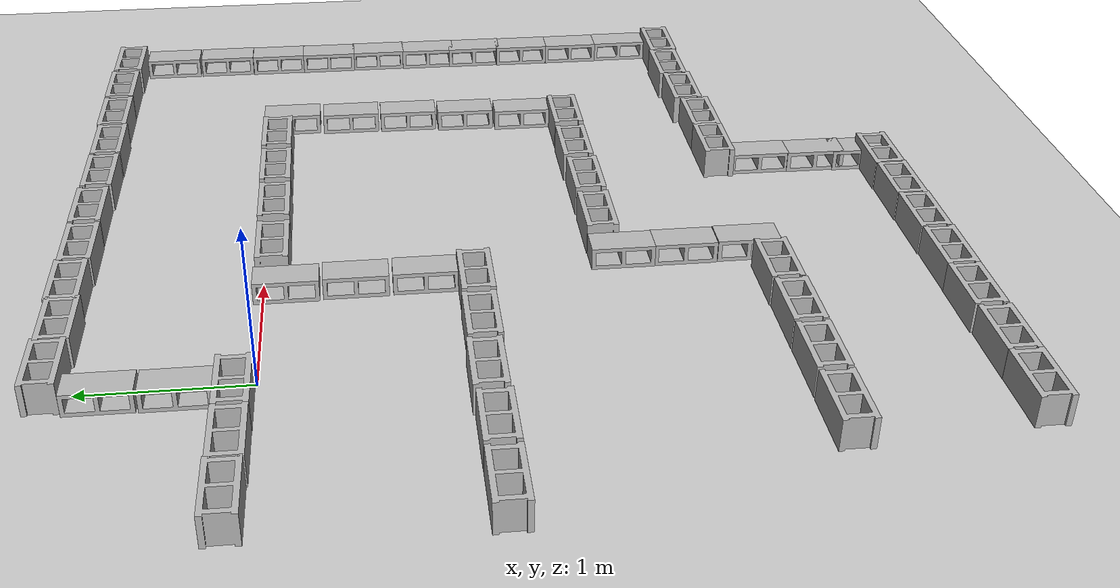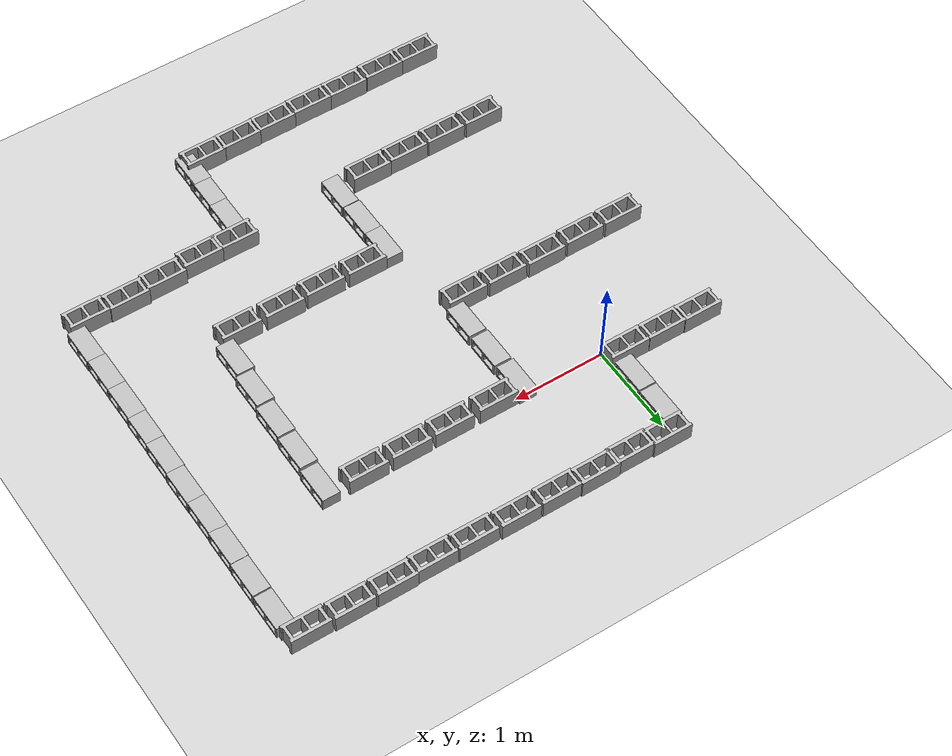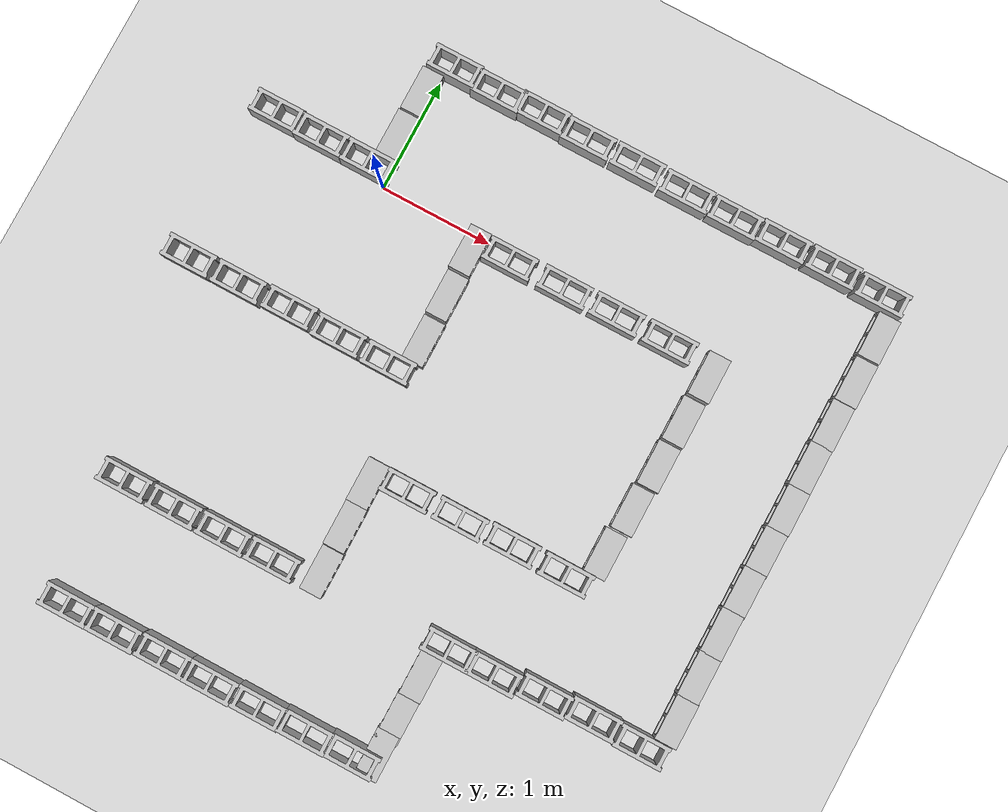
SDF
<sdf version="1.7">
 <world name="default">
  <light name="sun" type="directional">
   <pose>0 0 10 0 -0 0</pose>
   <diffuse>0.8 0.8 0.8 1</diffuse>
   <specular>0.2 0.2 0.2 1</specular>
   <attenuation>
    <range>1000</range>
    <constant>0.9</constant>
    <linear>0.01</linear>
    <quadratic>0.001</quadratic>
   </attenuation>
   <direction>-0.5 0.1 -0.9</direction>
   <spot><inner_angle>0</inner_angle><outer_angle>0</outer_angle><falloff>0</falloff></spot>
  </light>
  <model name="ground_plane">
   <static>1</static>
   <link name="link">
    <collision name="collision">
     <geometry><plane><normal>0 0 1</normal><size>100 100</size></plane></geometry>
     <surface>
      <contact><collide_bitmask>65535</collide_bitmask></contact>
      <friction><ode><mu>100</mu><mu2>50</mu2></ode></friction>
     </surface>
    </collision>
    <visual name="visual">
     <cast_shadows>0</cast_shadows>
     <geometry><plane><normal>0 0 1</normal><size>100 100</size></plane></geometry>
     <material>
      <script><uri>file://media/materials/scripts/gazebo.material</uri><name>Gazebo/Grey</name></script>
     </material>
    </visual>
   </link>
  </model>
  <gravity>0 0 -9.8</gravity>
  <magnetic_field>6e-06 2.3e-05 -4.2e-05</magnetic_field>
  <atmosphere type="adiabatic"/>
  <physics type="ode">
   <max_step_size>0.001</max_step_size>
   <real_time_factor>1</real_time_factor>
   <real_time_update_rate>1000</real_time_update_rate>
  </physics>
  <scene><ambient>0.4 0.4 0.4 1</ambient><background>0.7 0.7 0.7 1</background><shadows>1</shadows></scene>
  <audio><device>default</device></audio>
  <spherical_coordinates>
   <surface_model>EARTH_WGS84</surface_model>
   <latitude_deg>0</latitude_deg>
   <longitude_deg>0</longitude_deg>
   <elevation>0</elevation>
   <heading_deg>0</heading_deg>
  </spherical_coordinates>
  <model name="cinder_block">
   <link name="link">
    <inertial>
     <pose>0 0 0.1016 0 -0 0</pose>
     <mass>5</mass>
     <inertia>
      <ixx>0.028705</ixx>
      <ixy>0</ixy>
      <iyy>0.073708</iyy>
      <ixz>0</ixz>
      <iyz>0</iyz>
      <izz>0.06908</izz>
     </inertia>
    </inertial>
    <visual name="visual">
     <geometry><mesh><uri>model://cinder_block/meshes/cinder_block.dae</uri></mesh></geometry>
    </visual>
    <collision name="left">
     <pose>0 -0.08465 0.1016 0 -0 0</pose>
     <geometry><box><size>0.43495 0.0339 0.2032</size></box></geometry>
     <surface>
      <contact><ode><max_vel>0.1</max_vel><min_depth>0.001</min_depth></ode></contact>
      <friction><ode><mu>1</mu><mu2>1</mu2></ode></friction>
     </surface>
    </collision>
    <collision name="right">
     <pose>0 0.08465 0.1016 0 -0 0</pose>
     <geometry><box><size>0.43495 0.0339 0.2032</size></box></geometry>
     <surface>
      <contact><ode><max_vel>0.1</max_vel><min_depth>0.001</min_depth></ode></contact>
      <friction><ode><mu>1</mu><mu2>1</mu2></ode></friction>
     </surface>
    </collision>
    <collision name="front">
     <pose>0.18625 0 0.1016 0 -0 0</pose>
     <geometry><box><size>0.0339 0.1354 0.203</size></box></geometry>
     <surface>
      <contact><ode><max_vel>0.1</max_vel><min_depth>0.001</min_depth></ode></contact>
      <friction><ode><mu>1</mu><mu2>1</mu2></ode></friction>
     </surface>
    </collision>
    <collision name="middle">
     <pose>0 0 0.1016 0 -0 0</pose>
     <geometry><box><size>0.0339 0.1354 0.203</size></box></geometry>
     <surface>
      <contact><ode><max_vel>0.1</max_vel><min_depth>0.001</min_depth></ode></contact>
      <friction><ode><mu>1</mu><mu2>1</mu2></ode></friction>
     </surface>
    </collision>
    <collision name="back">
     <pose>-0.18625 0 0.1016 0 -0 0</pose>
     <geometry><box><size>0.0339 0.1354 0.203</size></box></geometry>
     <surface>
      <contact><ode><max_vel>0.1</max_vel><min_depth>0.001</min_depth></ode></contact>
      <friction><ode><mu>1</mu><mu2>1</mu2></ode></friction>
     </surface>
    </collision>
   </link>
   <pose>-0.166078 -1.2573 0 0 -0 0</pose>
  </model>
  <model name="cinder_block_0">
   <link name="link">
    <inertial>
     <pose>0 0 0.1016 0 -0 0</pose>
     <mass>5</mass>
     <inertia>
      <ixx>0.028705</ixx>
      <ixy>0</ixy>
      <iyy>0.073708</iyy>
      <ixz>0</ixz>
      <iyz>0</iyz>
      <izz>0.06908</izz>
     </inertia>
    </inertial>
    <visual name="visual">
     <geometry><mesh><uri>model://cinder_block/meshes/cinder_block.dae</uri></mesh></geometry>
    </visual>
    <collision name="left">
     <pose>0 -0.08465 0.1016 0 -0 0</pose>
     <geometry><box><size>0.43495 0.0339 0.2032</size></box></geometry>
     <surface>
      <contact><ode><max_vel>0.1</max_vel><min_depth>0.001</min_depth></ode></contact>
      <friction><ode><mu>1</mu><mu2>1</mu2></ode></friction>
     </surface>
    </collision>
    <collision name="right">
     <pose>0 0.08465 0.1016 0 -0 0</pose>
     <geometry><box><size>0.43495 0.0339 0.2032</size></box></geometry>
     <surface>
      <contact><ode><max_vel>0.1</max_vel><min_depth>0.001</min_depth></ode></contact>
      <friction><ode><mu>1</mu><mu2>1</mu2></ode></friction>
     </surface>
    </collision>
    <collision name="front">
     <pose>0.18625 0 0.1016 0 -0 0</pose>
     <geometry><box><size>0.0339 0.1354 0.203</size></box></geometry>
     <surface>
      <contact><ode><max_vel>0.1</max_vel><min_depth>0.001</min_depth></ode></contact>
      <friction><ode><mu>1</mu><mu2>1</mu2></ode></friction>
     </surface>
    </collision>
    <collision name="middle">
     <pose>0 0 0.1016 0 -0 0</pose>
     <geometry><box><size>0.0339 0.1354 0.203</size></box></geometry>
     <surface>
      <contact><ode><max_vel>0.1</max_vel><min_depth>0.001</min_depth></ode></contact>
      <friction><ode><mu>1</mu><mu2>1</mu2></ode></friction>
     </surface>
    </collision>
    <collision name="back">
     <pose>-0.18625 0 0.1016 0 -0 0</pose>
     <geometry><box><size>0.0339 0.1354 0.203</size></box></geometry>
     <surface>
      <contact><ode><max_vel>0.1</max_vel><min_depth>0.001</min_depth></ode></contact>
      <friction><ode><mu>1</mu><mu2>1</mu2></ode></friction>
     </surface>
    </collision>
   </link>
   <pose>-0.632446 -1.26918 0 0 -0 0</pose>
  </model>
  <model name="cinder_block_1">
   <link name="link">
    <inertial>
     <pose>0 0 0.1016 0 -0 0</pose>
     <mass>5</mass>
     <inertia>
      <ixx>0.028705</ixx>
      <ixy>0</ixy>
      <iyy>0.073708</iyy>
      <ixz>0</ixz>
      <iyz>0</iyz>
      <izz>0.06908</izz>
     </inertia>
    </inertial>
    <visual name="visual">
     <geometry><mesh><uri>model://cinder_block/meshes/cinder_block.dae</uri></mesh></geometry>
    </visual>
    <collision name="left">
     <pose>0 -0.08465 0.1016 0 -0 0</pose>
     <geometry><box><size>0.43495 0.0339 0.2032</size></box></geometry>
     <surface>
      <contact><ode><max_vel>0.1</max_vel><min_depth>0.001</min_depth></ode></contact>
      <friction><ode><mu>1</mu><mu2>1</mu2></ode></friction>
     </surface>
    </collision>
    <collision name="right">
     <pose>0 0.08465 0.1016 0 -0 0</pose>
     <geometry><box><size>0.43495 0.0339 0.2032</size></box></geometry>
     <surface>
      <contact><ode><max_vel>0.1</max_vel><min_depth>0.001</min_depth></ode></contact>
      <friction><ode><mu>1</mu><mu2>1</mu2></ode></friction>
     </surface>
    </collision>
    <collision name="front">
     <pose>0.18625 0 0.1016 0 -0 0</pose>
     <geometry><box><size>0.0339 0.1354 0.203</size></box></geometry>
     <surface>
      <contact><ode><max_vel>0.1</max_vel><min_depth>0.001</min_depth></ode></contact>
      <friction><ode><mu>1</mu><mu2>1</mu2></ode></friction>
     </surface>
    </collision>
    <collision name="middle">
     <pose>0 0 0.1016 0 -0 0</pose>
     <geometry><box><size>0.0339 0.1354 0.203</size></box></geometry>
     <surface>
      <contact><ode><max_vel>0.1</max_vel><min_depth>0.001</min_depth></ode></contact>
      <friction><ode><mu>1</mu><mu2>1</mu2></ode></friction>
     </surface>
    </collision>
    <collision name="back">
     <pose>-0.18625 0 0.1016 0 -0 0</pose>
     <geometry><box><size>0.0339 0.1354 0.203</size></box></geometry>
     <surface>
      <contact><ode><max_vel>0.1</max_vel><min_depth>0.001</min_depth></ode></contact>
      <friction><ode><mu>1</mu><mu2>1</mu2></ode></friction>
     </surface>
    </collision>
   </link>
   <pose>0.293561 -1.26789 0 0 -0 0</pose>
  </model>
  <model name="cinder_block_2">
   <link name="link">
    <inertial>
     <pose>0 0 0.1016 0 -0 0</pose>
     <mass>5</mass>
     <inertia>
      <ixx>0.028705</ixx>
      <ixy>0</ixy>
      <iyy>0.073708</iyy>
      <ixz>0</ixz>
      <iyz>0</iyz>
      <izz>0.06908</izz>
     </inertia>
    </inertial>
    <visual name="visual">
     <geometry><mesh><uri>model://cinder_block/meshes/cinder_block.dae</uri></mesh></geometry>
    </visual>
    <collision name="left">
     <pose>0 -0.08465 0.1016 0 -0 0</pose>
     <geometry><box><size>0.43495 0.0339 0.2032</size></box></geometry>
     <surface>
      <contact><ode><max_vel>0.1</max_vel><min_depth>0.001</min_depth></ode></contact>
      <friction><ode><mu>1</mu><mu2>1</mu2></ode></friction>
     </surface>
    </collision>
    <collision name="right">
     <pose>0 0.08465 0.1016 0 -0 0</pose>
     <geometry><box><size>0.43495 0.0339 0.2032</size></box></geometry>
     <surface>
      <contact><ode><max_vel>0.1</max_vel><min_depth>0.001</min_depth></ode></contact>
      <friction><ode><mu>1</mu><mu2>1</mu2></ode></friction>
     </surface>
    </collision>
    <collision name="front">
     <pose>0.18625 0 0.1016 0 -0 0</pose>
     <geometry><box><size>0.0339 0.1354 0.203</size></box></geometry>
     <surface>
      <contact><ode><max_vel>0.1</max_vel><min_depth>0.001</min_depth></ode></contact>
      <friction><ode><mu>1</mu><mu2>1</mu2></ode></friction>
     </surface>
    </collision>
    <collision name="middle">
     <pose>0 0 0.1016 0 -0 0</pose>
     <geometry><box><size>0.0339 0.1354 0.203</size></box></geometry>
     <surface>
      <contact><ode><max_vel>0.1</max_vel><min_depth>0.001</min_depth></ode></contact>
      <friction><ode><mu>1</mu><mu2>1</mu2></ode></friction>
     </surface>
    </collision>
    <collision name="back">
     <pose>-0.18625 0 0.1016 0 -0 0</pose>
     <geometry><box><size>0.0339 0.1354 0.203</size></box></geometry>
     <surface>
      <contact><ode><max_vel>0.1</max_vel><min_depth>0.001</min_depth></ode></contact>
      <friction><ode><mu>1</mu><mu2>1</mu2></ode></friction>
     </surface>
    </collision>
   </link>
   <pose>0.755754 -1.27256 0 0 -0 0</pose>
  </model>
  <model name="cinder_block_2_0">
   <link name="link">
    <inertial>
     <pose>0 0 0.071438 0 -0 0</pose>
     <mass>5</mass>
     <inertia>
      <ixx>0.06908</ixx>
      <ixy>0</ixy>
      <iyy>0.028705</iyy>
      <ixz>0</ixz>
      <iyz>0</iyz>
      <izz>0.073708</izz>
     </inertia>
    </inertial>
    <visual name="visual">
     <geometry><mesh><uri>model://cinder_block_2/meshes/cinder_block.dae</uri></mesh></geometry>
    </visual>
    <collision name="top">
     <pose>0 0 0.130175 0 -0 0</pose>
     <geometry><box><size>0.19368 0.396875 0.0254</size></box></geometry>
     <surface>
      <contact><ode><max_vel>0.1</max_vel><min_depth>0.001</min_depth></ode></contact>
      <friction><ode><mu>1</mu><mu2>1</mu2></ode></friction>
     </surface>
    </collision>
    <collision name="bottom">
     <pose>0 0 0.0127 0 -0 0</pose>
     <geometry><box><size>0.19368 0.396875 0.0254</size></box></geometry>
     <surface>
      <contact><ode><max_vel>0.1</max_vel><min_depth>0.001</min_depth></ode></contact>
      <friction><ode><mu>1</mu><mu2>1</mu2></ode></friction>
     </surface>
    </collision>
    <collision name="left">
     <pose>0 -0.185738 0.071438 0 -0 0</pose>
     <geometry><box><size>0.19368 0.0254 0.092075</size></box></geometry>
     <surface>
      <contact><ode><max_vel>0.1</max_vel><min_depth>0.001</min_depth></ode></contact>
      <friction><ode><mu>1</mu><mu2>1</mu2></ode></friction>
     </surface>
    </collision>
    <collision name="right">
     <pose>0 0.185738 0.071438 0 -0 0</pose>
     <geometry><box><size>0.19368 0.0254 0.092075</size></box></geometry>
     <surface>
      <contact><ode><max_vel>0.1</max_vel><min_depth>0.001</min_depth></ode></contact>
      <friction><ode><mu>1</mu><mu2>1</mu2></ode></friction>
     </surface>
    </collision>
    <collision name="middle">
     <pose>0 0 0.071438 0 -0 0</pose>
     <geometry><box><size>0.19368 0.0254 0.092075</size></box></geometry>
     <surface>
      <contact><ode><max_vel>0.1</max_vel><min_depth>0.001</min_depth></ode></contact>
      <friction><ode><mu>1</mu><mu2>1</mu2></ode></friction>
     </surface>
    </collision>
   </link>
   <pose>0.915039 -0.977644 0 0 -0 0</pose>
  </model>
  <model name="cinder_block_2_1">
   <link name="link">
    <inertial>
     <pose>0 0 0.071438 0 -0 0</pose>
     <mass>5</mass>
     <inertia>
      <ixx>0.06908</ixx>
      <ixy>0</ixy>
      <iyy>0.028705</iyy>
      <ixz>0</ixz>
      <iyz>0</iyz>
      <izz>0.073708</izz>
     </inertia>
    </inertial>
    <visual name="visual">
     <geometry><mesh><uri>model://cinder_block_2/meshes/cinder_block.dae</uri></mesh></geometry>
    </visual>
    <collision name="top">
     <pose>0 0 0.130175 0 -0 0</pose>
     <geometry><box><size>0.19368 0.396875 0.0254</size></box></geometry>
     <surface>
      <contact><ode><max_vel>0.1</max_vel><min_depth>0.001</min_depth></ode></contact>
      <friction><ode><mu>1</mu><mu2>1</mu2></ode></friction>
     </surface>
    </collision>
    <collision name="bottom">
     <pose>0 0 0.0127 0 -0 0</pose>
     <geometry><box><size>0.19368 0.396875 0.0254</size></box></geometry>
     <surface>
      <contact><ode><max_vel>0.1</max_vel><min_depth>0.001</min_depth></ode></contact>
      <friction><ode><mu>1</mu><mu2>1</mu2></ode></friction>
     </surface>
    </collision>
    <collision name="left">
     <pose>0 -0.185738 0.071438 0 -0 0</pose>
     <geometry><box><size>0.19368 0.0254 0.092075</size></box></geometry>
     <surface>
      <contact><ode><max_vel>0.1</max_vel><min_depth>0.001</min_depth></ode></contact>
      <friction><ode><mu>1</mu><mu2>1</mu2></ode></friction>
     </surface>
    </collision>
    <collision name="right">
     <pose>0 0.185738 0.071438 0 -0 0</pose>
     <geometry><box><size>0.19368 0.0254 0.092075</size></box></geometry>
     <surface>
      <contact><ode><max_vel>0.1</max_vel><min_depth>0.001</min_depth></ode></contact>
      <friction><ode><mu>1</mu><mu2>1</mu2></ode></friction>
     </surface>
    </collision>
    <collision name="middle">
     <pose>0 0 0.071438 0 -0 0</pose>
     <geometry><box><size>0.19368 0.0254 0.092075</size></box></geometry>
     <surface>
      <contact><ode><max_vel>0.1</max_vel><min_depth>0.001</min_depth></ode></contact>
      <friction><ode><mu>1</mu><mu2>1</mu2></ode></friction>
     </surface>
    </collision>
   </link>
   <pose>0.90795 -0.557757 0 0 -0 0</pose>
  </model>
  <model name="cinder_block_2_2">
   <link name="link">
    <inertial>
     <pose>0 0 0.071438 0 -0 0</pose>
     <mass>5</mass>
     <inertia>
      <ixx>0.06908</ixx>
      <ixy>0</ixy>
      <iyy>0.028705</iyy>
      <ixz>0</ixz>
      <iyz>0</iyz>
      <izz>0.073708</izz>
     </inertia>
    </inertial>
    <visual name="visual">
     <geometry><mesh><uri>model://cinder_block_2/meshes/cinder_block.dae</uri></mesh></geometry>
    </visual>
    <collision name="top">
     <pose>0 0 0.130175 0 -0 0</pose>
     <geometry><box><size>0.19368 0.396875 0.0254</size></box></geometry>
     <surface>
      <contact><ode><max_vel>0.1</max_vel><min_depth>0.001</min_depth></ode></contact>
      <friction><ode><mu>1</mu><mu2>1</mu2></ode></friction>
     </surface>
    </collision>
    <collision name="bottom">
     <pose>0 0 0.0127 0 -0 0</pose>
     <geometry><box><size>0.19368 0.396875 0.0254</size></box></geometry>
     <surface>
      <contact><ode><max_vel>0.1</max_vel><min_depth>0.001</min_depth></ode></contact>
      <friction><ode><mu>1</mu><mu2>1</mu2></ode></friction>
     </surface>
    </collision>
    <collision name="left">
     <pose>0 -0.185738 0.071438 0 -0 0</pose>
     <geometry><box><size>0.19368 0.0254 0.092075</size></box></geometry>
     <surface>
      <contact><ode><max_vel>0.1</max_vel><min_depth>0.001</min_depth></ode></contact>
      <friction><ode><mu>1</mu><mu2>1</mu2></ode></friction>
     </surface>
    </collision>
    <collision name="right">
     <pose>0 0.185738 0.071438 0 -0 0</pose>
     <geometry><box><size>0.19368 0.0254 0.092075</size></box></geometry>
     <surface>
      <contact><ode><max_vel>0.1</max_vel><min_depth>0.001</min_depth></ode></contact>
      <friction><ode><mu>1</mu><mu2>1</mu2></ode></friction>
     </surface>
    </collision>
    <collision name="middle">
     <pose>0 0 0.071438 0 -0 0</pose>
     <geometry><box><size>0.19368 0.0254 0.092075</size></box></geometry>
     <surface>
      <contact><ode><max_vel>0.1</max_vel><min_depth>0.001</min_depth></ode></contact>
      <friction><ode><mu>1</mu><mu2>1</mu2></ode></friction>
     </surface>
    </collision>
   </link>
   <pose>0.896648 -0.140806 0 0 -0 0</pose>
  </model>
  <model name="cinder_block_3">
   <link name="link">
    <inertial>
     <pose>0 0 0.1016 0 -0 0</pose>
     <mass>5</mass>
     <inertia>
      <ixx>0.028705</ixx>
      <ixy>0</ixy>
      <iyy>0.073708</iyy>
      <ixz>0</ixz>
      <iyz>0</iyz>
      <izz>0.06908</izz>
     </inertia>
    </inertial>
    <visual name="visual">
     <geometry><mesh><uri>model://cinder_block/meshes/cinder_block.dae</uri></mesh></geometry>
    </visual>
    <collision name="left">
     <pose>0 -0.08465 0.1016 0 -0 0</pose>
     <geometry><box><size>0.43495 0.0339 0.2032</size></box></geometry>
     <surface>
      <contact><ode><max_vel>0.1</max_vel><min_depth>0.001</min_depth></ode></contact>
      <friction><ode><mu>1</mu><mu2>1</mu2></ode></friction>
     </surface>
    </collision>
    <collision name="right">
     <pose>0 0.08465 0.1016 0 -0 0</pose>
     <geometry><box><size>0.43495 0.0339 0.2032</size></box></geometry>
     <surface>
      <contact><ode><max_vel>0.1</max_vel><min_depth>0.001</min_depth></ode></contact>
      <friction><ode><mu>1</mu><mu2>1</mu2></ode></friction>
     </surface>
    </collision>
    <collision name="front">
     <pose>0.18625 0 0.1016 0 -0 0</pose>
     <geometry><box><size>0.0339 0.1354 0.203</size></box></geometry>
     <surface>
      <contact><ode><max_vel>0.1</max_vel><min_depth>0.001</min_depth></ode></contact>
      <friction><ode><mu>1</mu><mu2>1</mu2></ode></friction>
     </surface>
    </collision>
    <collision name="middle">
     <pose>0 0 0.1016 0 -0 0</pose>
     <geometry><box><size>0.0339 0.1354 0.203</size></box></geometry>
     <surface>
      <contact><ode><max_vel>0.1</max_vel><min_depth>0.001</min_depth></ode></contact>
      <friction><ode><mu>1</mu><mu2>1</mu2></ode></friction>
     </surface>
    </collision>
    <collision name="back">
     <pose>-0.18625 0 0.1016 0 -0 0</pose>
     <geometry><box><size>0.0339 0.1354 0.203</size></box></geometry>
     <surface>
      <contact><ode><max_vel>0.1</max_vel><min_depth>0.001</min_depth></ode></contact>
      <friction><ode><mu>1</mu><mu2>1</mu2></ode></friction>
     </surface>
    </collision>
   </link>
   <pose>1.22059 -0.056694 0 0 -0 0</pose>
  </model>
  <model name="cinder_block_4">
   <link name="link">
    <inertial>
     <pose>0 0 0.1016 0 -0 0</pose>
     <mass>5</mass>
     <inertia>
      <ixx>0.028705</ixx>
      <ixy>0</ixy>
      <iyy>0.073708</iyy>
      <ixz>0</ixz>
      <iyz>0</iyz>
      <izz>0.06908</izz>
     </inertia>
    </inertial>
    <visual name="visual">
     <geometry><mesh><uri>model://cinder_block/meshes/cinder_block.dae</uri></mesh></geometry>
    </visual>
    <collision name="left">
     <pose>0 -0.08465 0.1016 0 -0 0</pose>
     <geometry><box><size>0.43495 0.0339 0.2032</size></box></geometry>
     <surface>
      <contact><ode><max_vel>0.1</max_vel><min_depth>0.001</min_depth></ode></contact>
      <friction><ode><mu>1</mu><mu2>1</mu2></ode></friction>
     </surface>
    </collision>
    <collision name="right">
     <pose>0 0.08465 0.1016 0 -0 0</pose>
     <geometry><box><size>0.43495 0.0339 0.2032</size></box></geometry>
     <surface>
      <contact><ode><max_vel>0.1</max_vel><min_depth>0.001</min_depth></ode></contact>
      <friction><ode><mu>1</mu><mu2>1</mu2></ode></friction>
     </surface>
    </collision>
    <collision name="front">
     <pose>0.18625 0 0.1016 0 -0 0</pose>
     <geometry><box><size>0.0339 0.1354 0.203</size></box></geometry>
     <surface>
      <contact><ode><max_vel>0.1</max_vel><min_depth>0.001</min_depth></ode></contact>
      <friction><ode><mu>1</mu><mu2>1</mu2></ode></friction>
     </surface>
    </collision>
    <collision name="middle">
     <pose>0 0 0.1016 0 -0 0</pose>
     <geometry><box><size>0.0339 0.1354 0.203</size></box></geometry>
     <surface>
      <contact><ode><max_vel>0.1</max_vel><min_depth>0.001</min_depth></ode></contact>
      <friction><ode><mu>1</mu><mu2>1</mu2></ode></friction>
     </surface>
    </collision>
    <collision name="back">
     <pose>-0.18625 0 0.1016 0 -0 0</pose>
     <geometry><box><size>0.0339 0.1354 0.203</size></box></geometry>
     <surface>
      <contact><ode><max_vel>0.1</max_vel><min_depth>0.001</min_depth></ode></contact>
      <friction><ode><mu>1</mu><mu2>1</mu2></ode></friction>
     </surface>
    </collision>
   </link>
   <pose>1.72291 -0.053168 0 0 -0 0</pose>
  </model>
  <model name="cinder_block_5">
   <link name="link">
    <inertial>
     <pose>0 0 0.1016 0 -0 0</pose>
     <mass>5</mass>
     <inertia>
      <ixx>0.028705</ixx>
      <ixy>0</ixy>
      <iyy>0.073708</iyy>
      <ixz>0</ixz>
      <iyz>0</iyz>
      <izz>0.06908</izz>
     </inertia>
    </inertial>
    <visual name="visual">
     <geometry><mesh><uri>model://cinder_block/meshes/cinder_block.dae</uri></mesh></geometry>
    </visual>
    <collision name="left">
     <pose>0 -0.08465 0.1016 0 -0 0</pose>
     <geometry><box><size>0.43495 0.0339 0.2032</size></box></geometry>
     <surface>
      <contact><ode><max_vel>0.1</max_vel><min_depth>0.001</min_depth></ode></contact>
      <friction><ode><mu>1</mu><mu2>1</mu2></ode></friction>
     </surface>
    </collision>
    <collision name="right">
     <pose>0 0.08465 0.1016 0 -0 0</pose>
     <geometry><box><size>0.43495 0.0339 0.2032</size></box></geometry>
     <surface>
      <contact><ode><max_vel>0.1</max_vel><min_depth>0.001</min_depth></ode></contact>
      <friction><ode><mu>1</mu><mu2>1</mu2></ode></friction>
     </surface>
    </collision>
    <collision name="front">
     <pose>0.18625 0 0.1016 0 -0 0</pose>
     <geometry><box><size>0.0339 0.1354 0.203</size></box></geometry>
     <surface>
      <contact><ode><max_vel>0.1</max_vel><min_depth>0.001</min_depth></ode></contact>
      <friction><ode><mu>1</mu><mu2>1</mu2></ode></friction>
     </surface>
    </collision>
    <collision name="middle">
     <pose>0 0 0.1016 0 -0 0</pose>
     <geometry><box><size>0.0339 0.1354 0.203</size></box></geometry>
     <surface>
      <contact><ode><max_vel>0.1</max_vel><min_depth>0.001</min_depth></ode></contact>
      <friction><ode><mu>1</mu><mu2>1</mu2></ode></friction>
     </surface>
    </collision>
    <collision name="back">
     <pose>-0.18625 0 0.1016 0 -0 0</pose>
     <geometry><box><size>0.0339 0.1354 0.203</size></box></geometry>
     <surface>
      <contact><ode><max_vel>0.1</max_vel><min_depth>0.001</min_depth></ode></contact>
      <friction><ode><mu>1</mu><mu2>1</mu2></ode></friction>
     </surface>
    </collision>
   </link>
   <pose>2.1997 -0.048204 0 0 -0 0</pose>
  </model>
  <model name="cinder_block_6">
   <link name="link">
    <inertial>
     <pose>0 0 0.1016 0 -0 0</pose>
     <mass>5</mass>
     <inertia>
      <ixx>0.028705</ixx>
      <ixy>0</ixy>
      <iyy>0.073708</iyy>
      <ixz>0</ixz>
      <iyz>0</iyz>
      <izz>0.06908</izz>
     </inertia>
    </inertial>
    <visual name="visual">
     <geometry><mesh><uri>model://cinder_block/meshes/cinder_block.dae</uri></mesh></geometry>
    </visual>
    <collision name="left">
     <pose>0 -0.08465 0.1016 0 -0 0</pose>
     <geometry><box><size>0.43495 0.0339 0.2032</size></box></geometry>
     <surface>
      <contact><ode><max_vel>0.1</max_vel><min_depth>0.001</min_depth></ode></contact>
      <friction><ode><mu>1</mu><mu2>1</mu2></ode></friction>
     </surface>
    </collision>
    <collision name="right">
     <pose>0 0.08465 0.1016 0 -0 0</pose>
     <geometry><box><size>0.43495 0.0339 0.2032</size></box></geometry>
     <surface>
      <contact><ode><max_vel>0.1</max_vel><min_depth>0.001</min_depth></ode></contact>
      <friction><ode><mu>1</mu><mu2>1</mu2></ode></friction>
     </surface>
    </collision>
    <collision name="front">
     <pose>0.18625 0 0.1016 0 -0 0</pose>
     <geometry><box><size>0.0339 0.1354 0.203</size></box></geometry>
     <surface>
      <contact><ode><max_vel>0.1</max_vel><min_depth>0.001</min_depth></ode></contact>
      <friction><ode><mu>1</mu><mu2>1</mu2></ode></friction>
     </surface>
    </collision>
    <collision name="middle">
     <pose>0 0 0.1016 0 -0 0</pose>
     <geometry><box><size>0.0339 0.1354 0.203</size></box></geometry>
     <surface>
      <contact><ode><max_vel>0.1</max_vel><min_depth>0.001</min_depth></ode></contact>
      <friction><ode><mu>1</mu><mu2>1</mu2></ode></friction>
     </surface>
    </collision>
    <collision name="back">
     <pose>-0.18625 0 0.1016 0 -0 0</pose>
     <geometry><box><size>0.0339 0.1354 0.203</size></box></geometry>
     <surface>
      <contact><ode><max_vel>0.1</max_vel><min_depth>0.001</min_depth></ode></contact>
      <friction><ode><mu>1</mu><mu2>1</mu2></ode></friction>
     </surface>
    </collision>
   </link>
   <pose>2.68308 -0.044089 0 0 -0 0</pose>
  </model>
  <model name="cinder_block_2_3">
   <link name="link">
    <inertial>
     <pose>0 0 0.071438 0 -0 0</pose>
     <mass>5</mass>
     <inertia>
      <ixx>0.06908</ixx>
      <ixy>0</ixy>
      <iyy>0.028705</iyy>
      <ixz>0</ixz>
      <iyz>0</iyz>
      <izz>0.073708</izz>
     </inertia>
    </inertial>
    <visual name="visual">
     <geometry><mesh><uri>model://cinder_block_2/meshes/cinder_block.dae</uri></mesh></geometry>
    </visual>
    <collision name="top">
     <pose>0 0 0.130175 0 -0 0</pose>
     <geometry><box><size>0.19368 0.396875 0.0254</size></box></geometry>
     <surface>
      <contact><ode><max_vel>0.1</max_vel><min_depth>0.001</min_depth></ode></contact>
      <friction><ode><mu>1</mu><mu2>1</mu2></ode></friction>
     </surface>
    </collision>
    <collision name="bottom">
     <pose>0 0 0.0127 0 -0 0</pose>
     <geometry><box><size>0.19368 0.396875 0.0254</size></box></geometry>
     <surface>
      <contact><ode><max_vel>0.1</max_vel><min_depth>0.001</min_depth></ode></contact>
      <friction><ode><mu>1</mu><mu2>1</mu2></ode></friction>
     </surface>
    </collision>
    <collision name="left">
     <pose>0 -0.185738 0.071438 0 -0 0</pose>
     <geometry><box><size>0.19368 0.0254 0.092075</size></box></geometry>
     <surface>
      <contact><ode><max_vel>0.1</max_vel><min_depth>0.001</min_depth></ode></contact>
      <friction><ode><mu>1</mu><mu2>1</mu2></ode></friction>
     </surface>
    </collision>
    <collision name="right">
     <pose>0 0.185738 0.071438 0 -0 0</pose>
     <geometry><box><size>0.19368 0.0254 0.092075</size></box></geometry>
     <surface>
      <contact><ode><max_vel>0.1</max_vel><min_depth>0.001</min_depth></ode></contact>
      <friction><ode><mu>1</mu><mu2>1</mu2></ode></friction>
     </surface>
    </collision>
    <collision name="middle">
     <pose>0 0 0.071438 0 -0 0</pose>
     <geometry><box><size>0.19368 0.0254 0.092075</size></box></geometry>
     <surface>
      <contact><ode><max_vel>0.1</max_vel><min_depth>0.001</min_depth></ode></contact>
      <friction><ode><mu>1</mu><mu2>1</mu2></ode></friction>
     </surface>
    </collision>
   </link>
   <pose>3.10302 -0.137854 0 0 -0 0</pose>
  </model>
  <model name="cinder_block_2_4">
   <link name="link">
    <inertial>
     <pose>0 0 0.071438 0 -0 0</pose>
     <mass>5</mass>
     <inertia>
      <ixx>0.06908</ixx>
      <ixy>0</ixy>
      <iyy>0.028705</iyy>
      <ixz>0</ixz>
      <iyz>0</iyz>
      <izz>0.073708</izz>
     </inertia>
    </inertial>
    <visual name="visual">
     <geometry><mesh><uri>model://cinder_block_2/meshes/cinder_block.dae</uri></mesh></geometry>
    </visual>
    <collision name="top">
     <pose>0 0 0.130175 0 -0 0</pose>
     <geometry><box><size>0.19368 0.396875 0.0254</size></box></geometry>
     <surface>
      <contact><ode><max_vel>0.1</max_vel><min_depth>0.001</min_depth></ode></contact>
      <friction><ode><mu>1</mu><mu2>1</mu2></ode></friction>
     </surface>
    </collision>
    <collision name="bottom">
     <pose>0 0 0.0127 0 -0 0</pose>
     <geometry><box><size>0.19368 0.396875 0.0254</size></box></geometry>
     <surface>
      <contact><ode><max_vel>0.1</max_vel><min_depth>0.001</min_depth></ode></contact>
      <friction><ode><mu>1</mu><mu2>1</mu2></ode></friction>
     </surface>
    </collision>
    <collision name="left">
     <pose>0 -0.185738 0.071438 0 -0 0</pose>
     <geometry><box><size>0.19368 0.0254 0.092075</size></box></geometry>
     <surface>
      <contact><ode><max_vel>0.1</max_vel><min_depth>0.001</min_depth></ode></contact>
      <friction><ode><mu>1</mu><mu2>1</mu2></ode></friction>
     </surface>
    </collision>
    <collision name="right">
     <pose>0 0.185738 0.071438 0 -0 0</pose>
     <geometry><box><size>0.19368 0.0254 0.092075</size></box></geometry>
     <surface>
      <contact><ode><max_vel>0.1</max_vel><min_depth>0.001</min_depth></ode></contact>
      <friction><ode><mu>1</mu><mu2>1</mu2></ode></friction>
     </surface>
    </collision>
    <collision name="middle">
     <pose>0 0 0.071438 0 -0 0</pose>
     <geometry><box><size>0.19368 0.0254 0.092075</size></box></geometry>
     <surface>
      <contact><ode><max_vel>0.1</max_vel><min_depth>0.001</min_depth></ode></contact>
      <friction><ode><mu>1</mu><mu2>1</mu2></ode></friction>
     </surface>
    </collision>
   </link>
   <pose>3.08683 -0.559179 0 0 -0 0</pose>
  </model>
  <model name="cinder_block_2_5">
   <link name="link">
    <inertial>
     <pose>0 0 0.071438 0 -0 0</pose>
     <mass>5</mass>
     <inertia>
      <ixx>0.06908</ixx>
      <ixy>0</ixy>
      <iyy>0.028705</iyy>
      <ixz>0</ixz>
      <iyz>0</iyz>
      <izz>0.073708</izz>
     </inertia>
    </inertial>
    <visual name="visual">
     <geometry><mesh><uri>model://cinder_block_2/meshes/cinder_block.dae</uri></mesh></geometry>
    </visual>
    <collision name="top">
     <pose>0 0 0.130175 0 -0 0</pose>
     <geometry><box><size>0.19368 0.396875 0.0254</size></box></geometry>
     <surface>
      <contact><ode><max_vel>0.1</max_vel><min_depth>0.001</min_depth></ode></contact>
      <friction><ode><mu>1</mu><mu2>1</mu2></ode></friction>
     </surface>
    </collision>
    <collision name="bottom">
     <pose>0 0 0.0127 0 -0 0</pose>
     <geometry><box><size>0.19368 0.396875 0.0254</size></box></geometry>
     <surface>
      <contact><ode><max_vel>0.1</max_vel><min_depth>0.001</min_depth></ode></contact>
      <friction><ode><mu>1</mu><mu2>1</mu2></ode></friction>
     </surface>
    </collision>
    <collision name="left">
     <pose>0 -0.185738 0.071438 0 -0 0</pose>
     <geometry><box><size>0.19368 0.0254 0.092075</size></box></geometry>
     <surface>
      <contact><ode><max_vel>0.1</max_vel><min_depth>0.001</min_depth></ode></contact>
      <friction><ode><mu>1</mu><mu2>1</mu2></ode></friction>
     </surface>
    </collision>
    <collision name="right">
     <pose>0 0.185738 0.071438 0 -0 0</pose>
     <geometry><box><size>0.19368 0.0254 0.092075</size></box></geometry>
     <surface>
      <contact><ode><max_vel>0.1</max_vel><min_depth>0.001</min_depth></ode></contact>
      <friction><ode><mu>1</mu><mu2>1</mu2></ode></friction>
     </surface>
    </collision>
    <collision name="middle">
     <pose>0 0 0.071438 0 -0 0</pose>
     <geometry><box><size>0.19368 0.0254 0.092075</size></box></geometry>
     <surface>
      <contact><ode><max_vel>0.1</max_vel><min_depth>0.001</min_depth></ode></contact>
      <friction><ode><mu>1</mu><mu2>1</mu2></ode></friction>
     </surface>
    </collision>
   </link>
   <pose>3.07753 -0.973132 0 0 -0 0</pose>
  </model>
  <model name="cinder_block_2_6">
   <link name="link">
    <inertial>
     <pose>0 0 0.071438 0 -0 0</pose>
     <mass>5</mass>
     <inertia>
      <ixx>0.06908</ixx>
      <ixy>0</ixy>
      <iyy>0.028705</iyy>
      <ixz>0</ixz>
      <iyz>0</iyz>
      <izz>0.073708</izz>
     </inertia>
    </inertial>
    <visual name="visual">
     <geometry><mesh><uri>model://cinder_block_2/meshes/cinder_block.dae</uri></mesh></geometry>
    </visual>
    <collision name="top">
     <pose>0 0 0.130175 0 -0 0</pose>
     <geometry><box><size>0.19368 0.396875 0.0254</size></box></geometry>
     <surface>
      <contact><ode><max_vel>0.1</max_vel><min_depth>0.001</min_depth></ode></contact>
      <friction><ode><mu>1</mu><mu2>1</mu2></ode></friction>
     </surface>
    </collision>
    <collision name="bottom">
     <pose>0 0 0.0127 0 -0 0</pose>
     <geometry><box><size>0.19368 0.396875 0.0254</size></box></geometry>
     <surface>
      <contact><ode><max_vel>0.1</max_vel><min_depth>0.001</min_depth></ode></contact>
      <friction><ode><mu>1</mu><mu2>1</mu2></ode></friction>
     </surface>
    </collision>
    <collision name="left">
     <pose>0 -0.185738 0.071438 0 -0 0</pose>
     <geometry><box><size>0.19368 0.0254 0.092075</size></box></geometry>
     <surface>
      <contact><ode><max_vel>0.1</max_vel><min_depth>0.001</min_depth></ode></contact>
      <friction><ode><mu>1</mu><mu2>1</mu2></ode></friction>
     </surface>
    </collision>
    <collision name="right">
     <pose>0 0.185738 0.071438 0 -0 0</pose>
     <geometry><box><size>0.19368 0.0254 0.092075</size></box></geometry>
     <surface>
      <contact><ode><max_vel>0.1</max_vel><min_depth>0.001</min_depth></ode></contact>
      <friction><ode><mu>1</mu><mu2>1</mu2></ode></friction>
     </surface>
    </collision>
    <collision name="middle">
     <pose>0 0 0.071438 0 -0 0</pose>
     <geometry><box><size>0.19368 0.0254 0.092075</size></box></geometry>
     <surface>
      <contact><ode><max_vel>0.1</max_vel><min_depth>0.001</min_depth></ode></contact>
      <friction><ode><mu>1</mu><mu2>1</mu2></ode></friction>
     </surface>
    </collision>
   </link>
   <pose>3.05506 -1.38687 0 0 -0 0</pose>
  </model>
  <model name="cinder_block_2_7">
   <link name="link">
    <inertial>
     <pose>0 0 0.071438 0 -0 0</pose>
     <mass>5</mass>
     <inertia>
      <ixx>0.06908</ixx>
      <ixy>0</ixy>
      <iyy>0.028705</iyy>
      <ixz>0</ixz>
      <iyz>0</iyz>
      <izz>0.073708</izz>
     </inertia>
    </inertial>
    <visual name="visual">
     <geometry><mesh><uri>model://cinder_block_2/meshes/cinder_block.dae</uri></mesh></geometry>
    </visual>
    <collision name="top">
     <pose>0 0 0.130175 0 -0 0</pose>
     <geometry><box><size>0.19368 0.396875 0.0254</size></box></geometry>
     <surface>
      <contact><ode><max_vel>0.1</max_vel><min_depth>0.001</min_depth></ode></contact>
      <friction><ode><mu>1</mu><mu2>1</mu2></ode></friction>
     </surface>
    </collision>
    <collision name="bottom">
     <pose>0 0 0.0127 0 -0 0</pose>
     <geometry><box><size>0.19368 0.396875 0.0254</size></box></geometry>
     <surface>
      <contact><ode><max_vel>0.1</max_vel><min_depth>0.001</min_depth></ode></contact>
      <friction><ode><mu>1</mu><mu2>1</mu2></ode></friction>
     </surface>
    </collision>
    <collision name="left">
     <pose>0 -0.185738 0.071438 0 -0 0</pose>
     <geometry><box><size>0.19368 0.0254 0.092075</size></box></geometry>
     <surface>
      <contact><ode><max_vel>0.1</max_vel><min_depth>0.001</min_depth></ode></contact>
      <friction><ode><mu>1</mu><mu2>1</mu2></ode></friction>
     </surface>
    </collision>
    <collision name="right">
     <pose>0 0.185738 0.071438 0 -0 0</pose>
     <geometry><box><size>0.19368 0.0254 0.092075</size></box></geometry>
     <surface>
      <contact><ode><max_vel>0.1</max_vel><min_depth>0.001</min_depth></ode></contact>
      <friction><ode><mu>1</mu><mu2>1</mu2></ode></friction>
     </surface>
    </collision>
    <collision name="middle">
     <pose>0 0 0.071438 0 -0 0</pose>
     <geometry><box><size>0.19368 0.0254 0.092075</size></box></geometry>
     <surface>
      <contact><ode><max_vel>0.1</max_vel><min_depth>0.001</min_depth></ode></contact>
      <friction><ode><mu>1</mu><mu2>1</mu2></ode></friction>
     </surface>
    </collision>
   </link>
   <pose>3.02606 -1.79977 0 0 -0 0</pose>
  </model>
  <model name="cinder_block_7">
   <link name="link">
    <inertial>
     <pose>0 0 0.1016 0 -0 0</pose>
     <mass>5</mass>
     <inertia>
      <ixx>0.028705</ixx>
      <ixy>0</ixy>
      <iyy>0.073708</iyy>
      <ixz>0</ixz>
      <iyz>0</iyz>
      <izz>0.06908</izz>
     </inertia>
    </inertial>
    <visual name="visual">
     <geometry><mesh><uri>model://cinder_block/meshes/cinder_block.dae</uri></mesh></geometry>
    </visual>
    <collision name="left">
     <pose>0 -0.08465 0.1016 0 -0 0</pose>
     <geometry><box><size>0.43495 0.0339 0.2032</size></box></geometry>
     <surface>
      <contact><ode><max_vel>0.1</max_vel><min_depth>0.001</min_depth></ode></contact>
      <friction><ode><mu>1</mu><mu2>1</mu2></ode></friction>
     </surface>
    </collision>
    <collision name="right">
     <pose>0 0.08465 0.1016 0 -0 0</pose>
     <geometry><box><size>0.43495 0.0339 0.2032</size></box></geometry>
     <surface>
      <contact><ode><max_vel>0.1</max_vel><min_depth>0.001</min_depth></ode></contact>
      <friction><ode><mu>1</mu><mu2>1</mu2></ode></friction>
     </surface>
    </collision>
    <collision name="front">
     <pose>0.18625 0 0.1016 0 -0 0</pose>
     <geometry><box><size>0.0339 0.1354 0.203</size></box></geometry>
     <surface>
      <contact><ode><max_vel>0.1</max_vel><min_depth>0.001</min_depth></ode></contact>
      <friction><ode><mu>1</mu><mu2>1</mu2></ode></friction>
     </surface>
    </collision>
    <collision name="middle">
     <pose>0 0 0.1016 0 -0 0</pose>
     <geometry><box><size>0.0339 0.1354 0.203</size></box></geometry>
     <surface>
      <contact><ode><max_vel>0.1</max_vel><min_depth>0.001</min_depth></ode></contact>
      <friction><ode><mu>1</mu><mu2>1</mu2></ode></friction>
     </surface>
    </collision>
    <collision name="back">
     <pose>-0.18625 0 0.1016 0 -0 0</pose>
     <geometry><box><size>0.0339 0.1354 0.203</size></box></geometry>
     <surface>
      <contact><ode><max_vel>0.1</max_vel><min_depth>0.001</min_depth></ode></contact>
      <friction><ode><mu>1</mu><mu2>1</mu2></ode></friction>
     </surface>
    </collision>
   </link>
   <pose>2.82138 -2.09674 0 0 -0 0</pose>
  </model>
  <model name="cinder_block_8">
   <link name="link">
    <inertial>
     <pose>0 0 0.1016 0 -0 0</pose>
     <mass>5</mass>
     <inertia>
      <ixx>0.028705</ixx>
      <ixy>0</ixy>
      <iyy>0.073708</iyy>
      <ixz>0</ixz>
      <iyz>0</iyz>
      <izz>0.06908</izz>
     </inertia>
    </inertial>
    <visual name="visual">
     <geometry><mesh><uri>model://cinder_block/meshes/cinder_block.dae</uri></mesh></geometry>
    </visual>
    <collision name="left">
     <pose>0 -0.08465 0.1016 0 -0 0</pose>
     <geometry><box><size>0.43495 0.0339 0.2032</size></box></geometry>
     <surface>
      <contact><ode><max_vel>0.1</max_vel><min_depth>0.001</min_depth></ode></contact>
      <friction><ode><mu>1</mu><mu2>1</mu2></ode></friction>
     </surface>
    </collision>
    <collision name="right">
     <pose>0 0.08465 0.1016 0 -0 0</pose>
     <geometry><box><size>0.43495 0.0339 0.2032</size></box></geometry>
     <surface>
      <contact><ode><max_vel>0.1</max_vel><min_depth>0.001</min_depth></ode></contact>
      <friction><ode><mu>1</mu><mu2>1</mu2></ode></friction>
     </surface>
    </collision>
    <collision name="front">
     <pose>0.18625 0 0.1016 0 -0 0</pose>
     <geometry><box><size>0.0339 0.1354 0.203</size></box></geometry>
     <surface>
      <contact><ode><max_vel>0.1</max_vel><min_depth>0.001</min_depth></ode></contact>
      <friction><ode><mu>1</mu><mu2>1</mu2></ode></friction>
     </surface>
    </collision>
    <collision name="middle">
     <pose>0 0 0.1016 0 -0 0</pose>
     <geometry><box><size>0.0339 0.1354 0.203</size></box></geometry>
     <surface>
      <contact><ode><max_vel>0.1</max_vel><min_depth>0.001</min_depth></ode></contact>
      <friction><ode><mu>1</mu><mu2>1</mu2></ode></friction>
     </surface>
    </collision>
    <collision name="back">
     <pose>-0.18625 0 0.1016 0 -0 0</pose>
     <geometry><box><size>0.0339 0.1354 0.203</size></box></geometry>
     <surface>
      <contact><ode><max_vel>0.1</max_vel><min_depth>0.001</min_depth></ode></contact>
      <friction><ode><mu>1</mu><mu2>1</mu2></ode></friction>
     </surface>
    </collision>
   </link>
   <pose>2.33341 -2.09364 0 0 -0 0</pose>
  </model>
  <model name="cinder_block_9">
   <link name="link">
    <inertial>
     <pose>0 0 0.1016 0 -0 0</pose>
     <mass>5</mass>
     <inertia>
      <ixx>0.028705</ixx>
      <ixy>0</ixy>
      <iyy>0.073708</iyy>
      <ixz>0</ixz>
      <iyz>0</iyz>
      <izz>0.06908</izz>
     </inertia>
    </inertial>
    <visual name="visual">
     <geometry><mesh><uri>model://cinder_block/meshes/cinder_block.dae</uri></mesh></geometry>
    </visual>
    <collision name="left">
     <pose>0 -0.08465 0.1016 0 -0 0</pose>
     <geometry><box><size>0.43495 0.0339 0.2032</size></box></geometry>
     <surface>
      <contact><ode><max_vel>0.1</max_vel><min_depth>0.001</min_depth></ode></contact>
      <friction><ode><mu>1</mu><mu2>1</mu2></ode></friction>
     </surface>
    </collision>
    <collision name="right">
     <pose>0 0.08465 0.1016 0 -0 0</pose>
     <geometry><box><size>0.43495 0.0339 0.2032</size></box></geometry>
     <surface>
      <contact><ode><max_vel>0.1</max_vel><min_depth>0.001</min_depth></ode></contact>
      <friction><ode><mu>1</mu><mu2>1</mu2></ode></friction>
     </surface>
    </collision>
    <collision name="front">
     <pose>0.18625 0 0.1016 0 -0 0</pose>
     <geometry><box><size>0.0339 0.1354 0.203</size></box></geometry>
     <surface>
      <contact><ode><max_vel>0.1</max_vel><min_depth>0.001</min_depth></ode></contact>
      <friction><ode><mu>1</mu><mu2>1</mu2></ode></friction>
     </surface>
    </collision>
    <collision name="middle">
     <pose>0 0 0.1016 0 -0 0</pose>
     <geometry><box><size>0.0339 0.1354 0.203</size></box></geometry>
     <surface>
      <contact><ode><max_vel>0.1</max_vel><min_depth>0.001</min_depth></ode></contact>
      <friction><ode><mu>1</mu><mu2>1</mu2></ode></friction>
     </surface>
    </collision>
    <collision name="back">
     <pose>-0.18625 0 0.1016 0 -0 0</pose>
     <geometry><box><size>0.0339 0.1354 0.203</size></box></geometry>
     <surface>
      <contact><ode><max_vel>0.1</max_vel><min_depth>0.001</min_depth></ode></contact>
      <friction><ode><mu>1</mu><mu2>1</mu2></ode></friction>
     </surface>
    </collision>
   </link>
   <pose>1.86528 -2.10568 0 0 -0 0</pose>
  </model>
  <model name="cinder_block_10">
   <link name="link">
    <inertial>
     <pose>0 0 0.1016 0 -0 0</pose>
     <mass>5</mass>
     <inertia>
      <ixx>0.028705</ixx>
      <ixy>0</ixy>
      <iyy>0.073708</iyy>
      <ixz>0</ixz>
      <iyz>0</iyz>
      <izz>0.06908</izz>
     </inertia>
    </inertial>
    <visual name="visual">
     <geometry><mesh><uri>model://cinder_block/meshes/cinder_block.dae</uri></mesh></geometry>
    </visual>
    <collision name="left">
     <pose>0 -0.08465 0.1016 0 -0 0</pose>
     <geometry><box><size>0.43495 0.0339 0.2032</size></box></geometry>
     <surface>
      <contact><ode><max_vel>0.1</max_vel><min_depth>0.001</min_depth></ode></contact>
      <friction><ode><mu>1</mu><mu2>1</mu2></ode></friction>
     </surface>
    </collision>
    <collision name="right">
     <pose>0 0.08465 0.1016 0 -0 0</pose>
     <geometry><box><size>0.43495 0.0339 0.2032</size></box></geometry>
     <surface>
      <contact><ode><max_vel>0.1</max_vel><min_depth>0.001</min_depth></ode></contact>
      <friction><ode><mu>1</mu><mu2>1</mu2></ode></friction>
     </surface>
    </collision>
    <collision name="front">
     <pose>0.18625 0 0.1016 0 -0 0</pose>
     <geometry><box><size>0.0339 0.1354 0.203</size></box></geometry>
     <surface>
      <contact><ode><max_vel>0.1</max_vel><min_depth>0.001</min_depth></ode></contact>
      <friction><ode><mu>1</mu><mu2>1</mu2></ode></friction>
     </surface>
    </collision>
    <collision name="middle">
     <pose>0 0 0.1016 0 -0 0</pose>
     <geometry><box><size>0.0339 0.1354 0.203</size></box></geometry>
     <surface>
      <contact><ode><max_vel>0.1</max_vel><min_depth>0.001</min_depth></ode></contact>
      <friction><ode><mu>1</mu><mu2>1</mu2></ode></friction>
     </surface>
    </collision>
    <collision name="back">
     <pose>-0.18625 0 0.1016 0 -0 0</pose>
     <geometry><box><size>0.0339 0.1354 0.203</size></box></geometry>
     <surface>
      <contact><ode><max_vel>0.1</max_vel><min_depth>0.001</min_depth></ode></contact>
      <friction><ode><mu>1</mu><mu2>1</mu2></ode></friction>
     </surface>
    </collision>
   </link>
   <pose>1.38491 -2.10697 0 0 -0 0</pose>
  </model>
  <model name="cinder_block_2_8">
   <link name="link">
    <inertial>
     <pose>0 0 0.071438 0 -0 0</pose>
     <mass>5</mass>
     <inertia>
      <ixx>0.06908</ixx>
      <ixy>0</ixy>
      <iyy>0.028705</iyy>
      <ixz>0</ixz>
      <iyz>0</iyz>
      <izz>0.073708</izz>
     </inertia>
    </inertial>
    <visual name="visual">
     <geometry><mesh><uri>model://cinder_block_2/meshes/cinder_block.dae</uri></mesh></geometry>
    </visual>
    <collision name="top">
     <pose>0 0 0.130175 0 -0 0</pose>
     <geometry><box><size>0.19368 0.396875 0.0254</size></box></geometry>
     <surface>
      <contact><ode><max_vel>0.1</max_vel><min_depth>0.001</min_depth></ode></contact>
      <friction><ode><mu>1</mu><mu2>1</mu2></ode></friction>
     </surface>
    </collision>
    <collision name="bottom">
     <pose>0 0 0.0127 0 -0 0</pose>
     <geometry><box><size>0.19368 0.396875 0.0254</size></box></geometry>
     <surface>
      <contact><ode><max_vel>0.1</max_vel><min_depth>0.001</min_depth></ode></contact>
      <friction><ode><mu>1</mu><mu2>1</mu2></ode></friction>
     </surface>
    </collision>
    <collision name="left">
     <pose>0 -0.185738 0.071438 0 -0 0</pose>
     <geometry><box><size>0.19368 0.0254 0.092075</size></box></geometry>
     <surface>
      <contact><ode><max_vel>0.1</max_vel><min_depth>0.001</min_depth></ode></contact>
      <friction><ode><mu>1</mu><mu2>1</mu2></ode></friction>
     </surface>
    </collision>
    <collision name="right">
     <pose>0 0.185738 0.071438 0 -0 0</pose>
     <geometry><box><size>0.19368 0.0254 0.092075</size></box></geometry>
     <surface>
      <contact><ode><max_vel>0.1</max_vel><min_depth>0.001</min_depth></ode></contact>
      <friction><ode><mu>1</mu><mu2>1</mu2></ode></friction>
     </surface>
    </collision>
    <collision name="middle">
     <pose>0 0 0.071438 0 -0 0</pose>
     <geometry><box><size>0.19368 0.0254 0.092075</size></box></geometry>
     <surface>
      <contact><ode><max_vel>0.1</max_vel><min_depth>0.001</min_depth></ode></contact>
      <friction><ode><mu>1</mu><mu2>1</mu2></ode></friction>
     </surface>
    </collision>
   </link>
   <pose>1.07228 -2.20784 0 0 -0 0</pose>
  </model>
  <model name="cinder_block_2_9">
   <link name="link">
    <inertial>
     <pose>0 0 0.071438 0 -0 0</pose>
     <mass>5</mass>
     <inertia>
      <ixx>0.06908</ixx>
      <ixy>0</ixy>
      <iyy>0.028705</iyy>
      <ixz>0</ixz>
      <iyz>0</iyz>
      <izz>0.073708</izz>
     </inertia>
    </inertial>
    <visual name="visual">
     <geometry><mesh><uri>model://cinder_block_2/meshes/cinder_block.dae</uri></mesh></geometry>
    </visual>
    <collision name="top">
     <pose>0 0 0.130175 0 -0 0</pose>
     <geometry><box><size>0.19368 0.396875 0.0254</size></box></geometry>
     <surface>
      <contact><ode><max_vel>0.1</max_vel><min_depth>0.001</min_depth></ode></contact>
      <friction><ode><mu>1</mu><mu2>1</mu2></ode></friction>
     </surface>
    </collision>
    <collision name="bottom">
     <pose>0 0 0.0127 0 -0 0</pose>
     <geometry><box><size>0.19368 0.396875 0.0254</size></box></geometry>
     <surface>
      <contact><ode><max_vel>0.1</max_vel><min_depth>0.001</min_depth></ode></contact>
      <friction><ode><mu>1</mu><mu2>1</mu2></ode></friction>
     </surface>
    </collision>
    <collision name="left">
     <pose>0 -0.185738 0.071438 0 -0 0</pose>
     <geometry><box><size>0.19368 0.0254 0.092075</size></box></geometry>
     <surface>
      <contact><ode><max_vel>0.1</max_vel><min_depth>0.001</min_depth></ode></contact>
      <friction><ode><mu>1</mu><mu2>1</mu2></ode></friction>
     </surface>
    </collision>
    <collision name="right">
     <pose>0 0.185738 0.071438 0 -0 0</pose>
     <geometry><box><size>0.19368 0.0254 0.092075</size></box></geometry>
     <surface>
      <contact><ode><max_vel>0.1</max_vel><min_depth>0.001</min_depth></ode></contact>
      <friction><ode><mu>1</mu><mu2>1</mu2></ode></friction>
     </surface>
    </collision>
    <collision name="middle">
     <pose>0 0 0.071438 0 -0 0</pose>
     <geometry><box><size>0.19368 0.0254 0.092075</size></box></geometry>
     <surface>
      <contact><ode><max_vel>0.1</max_vel><min_depth>0.001</min_depth></ode></contact>
      <friction><ode><mu>1</mu><mu2>1</mu2></ode></friction>
     </surface>
    </collision>
   </link>
   <pose>1.07664 -2.60128 0 0 -0 0</pose>
  </model>
  <model name="cinder_block_2_10">
   <link name="link">
    <inertial>
     <pose>0 0 0.071438 0 -0 0</pose>
     <mass>5</mass>
     <inertia>
      <ixx>0.06908</ixx>
      <ixy>0</ixy>
      <iyy>0.028705</iyy>
      <ixz>0</ixz>
      <iyz>0</iyz>
      <izz>0.073708</izz>
     </inertia>
    </inertial>
    <visual name="visual">
     <geometry><mesh><uri>model://cinder_block_2/meshes/cinder_block.dae</uri></mesh></geometry>
    </visual>
    <collision name="top">
     <pose>0 0 0.130175 0 -0 0</pose>
     <geometry><box><size>0.19368 0.396875 0.0254</size></box></geometry>
     <surface>
      <contact><ode><max_vel>0.1</max_vel><min_depth>0.001</min_depth></ode></contact>
      <friction><ode><mu>1</mu><mu2>1</mu2></ode></friction>
     </surface>
    </collision>
    <collision name="bottom">
     <pose>0 0 0.0127 0 -0 0</pose>
     <geometry><box><size>0.19368 0.396875 0.0254</size></box></geometry>
     <surface>
      <contact><ode><max_vel>0.1</max_vel><min_depth>0.001</min_depth></ode></contact>
      <friction><ode><mu>1</mu><mu2>1</mu2></ode></friction>
     </surface>
    </collision>
    <collision name="left">
     <pose>0 -0.185738 0.071438 0 -0 0</pose>
     <geometry><box><size>0.19368 0.0254 0.092075</size></box></geometry>
     <surface>
      <contact><ode><max_vel>0.1</max_vel><min_depth>0.001</min_depth></ode></contact>
      <friction><ode><mu>1</mu><mu2>1</mu2></ode></friction>
     </surface>
    </collision>
    <collision name="right">
     <pose>0 0.185738 0.071438 0 -0 0</pose>
     <geometry><box><size>0.19368 0.0254 0.092075</size></box></geometry>
     <surface>
      <contact><ode><max_vel>0.1</max_vel><min_depth>0.001</min_depth></ode></contact>
      <friction><ode><mu>1</mu><mu2>1</mu2></ode></friction>
     </surface>
    </collision>
    <collision name="middle">
     <pose>0 0 0.071438 0 -0 0</pose>
     <geometry><box><size>0.19368 0.0254 0.092075</size></box></geometry>
     <surface>
      <contact><ode><max_vel>0.1</max_vel><min_depth>0.001</min_depth></ode></contact>
      <friction><ode><mu>1</mu><mu2>1</mu2></ode></friction>
     </surface>
    </collision>
   </link>
   <pose>1.08379 -3.00331 0 0 -0 0</pose>
  </model>
  <model name="cinder_block_11">
   <link name="link">
    <inertial>
     <pose>0 0 0.1016 0 -0 0</pose>
     <mass>5</mass>
     <inertia>
      <ixx>0.028705</ixx>
      <ixy>0</ixy>
      <iyy>0.073708</iyy>
      <ixz>0</ixz>
      <iyz>0</iyz>
      <izz>0.06908</izz>
     </inertia>
    </inertial>
    <visual name="visual">
     <geometry><mesh><uri>model://cinder_block/meshes/cinder_block.dae</uri></mesh></geometry>
    </visual>
    <collision name="left">
     <pose>0 -0.08465 0.1016 0 -0 0</pose>
     <geometry><box><size>0.43495 0.0339 0.2032</size></box></geometry>
     <surface>
      <contact><ode><max_vel>0.1</max_vel><min_depth>0.001</min_depth></ode></contact>
      <friction><ode><mu>1</mu><mu2>1</mu2></ode></friction>
     </surface>
    </collision>
    <collision name="right">
     <pose>0 0.08465 0.1016 0 -0 0</pose>
     <geometry><box><size>0.43495 0.0339 0.2032</size></box></geometry>
     <surface>
      <contact><ode><max_vel>0.1</max_vel><min_depth>0.001</min_depth></ode></contact>
      <friction><ode><mu>1</mu><mu2>1</mu2></ode></friction>
     </surface>
    </collision>
    <collision name="front">
     <pose>0.18625 0 0.1016 0 -0 0</pose>
     <geometry><box><size>0.0339 0.1354 0.203</size></box></geometry>
     <surface>
      <contact><ode><max_vel>0.1</max_vel><min_depth>0.001</min_depth></ode></contact>
      <friction><ode><mu>1</mu><mu2>1</mu2></ode></friction>
     </surface>
    </collision>
    <collision name="middle">
     <pose>0 0 0.1016 0 -0 0</pose>
     <geometry><box><size>0.0339 0.1354 0.203</size></box></geometry>
     <surface>
      <contact><ode><max_vel>0.1</max_vel><min_depth>0.001</min_depth></ode></contact>
      <friction><ode><mu>1</mu><mu2>1</mu2></ode></friction>
     </surface>
    </collision>
    <collision name="back">
     <pose>-0.18625 0 0.1016 0 -0 0</pose>
     <geometry><box><size>0.0339 0.1354 0.203</size></box></geometry>
     <surface>
      <contact><ode><max_vel>0.1</max_vel><min_depth>0.001</min_depth></ode></contact>
      <friction><ode><mu>1</mu><mu2>1</mu2></ode></friction>
     </surface>
    </collision>
   </link>
   <pose>0.692084 -3.10191 0 0 -0 0</pose>
  </model>
  <model name="cinder_block_12">
   <link name="link">
    <inertial>
     <pose>0 0 0.1016 0 -0 0</pose>
     <mass>5</mass>
     <inertia>
      <ixx>0.028705</ixx>
      <ixy>0</ixy>
      <iyy>0.073708</iyy>
      <ixz>0</ixz>
      <iyz>0</iyz>
      <izz>0.06908</izz>
     </inertia>
    </inertial>
    <visual name="visual">
     <geometry><mesh><uri>model://cinder_block/meshes/cinder_block.dae</uri></mesh></geometry>
    </visual>
    <collision name="left">
     <pose>0 -0.08465 0.1016 0 -0 0</pose>
     <geometry><box><size>0.43495 0.0339 0.2032</size></box></geometry>
     <surface>
      <contact><ode><max_vel>0.1</max_vel><min_depth>0.001</min_depth></ode></contact>
      <friction><ode><mu>1</mu><mu2>1</mu2></ode></friction>
     </surface>
    </collision>
    <collision name="right">
     <pose>0 0.08465 0.1016 0 -0 0</pose>
     <geometry><box><size>0.43495 0.0339 0.2032</size></box></geometry>
     <surface>
      <contact><ode><max_vel>0.1</max_vel><min_depth>0.001</min_depth></ode></contact>
      <friction><ode><mu>1</mu><mu2>1</mu2></ode></friction>
     </surface>
    </collision>
    <collision name="front">
     <pose>0.18625 0 0.1016 0 -0 0</pose>
     <geometry><box><size>0.0339 0.1354 0.203</size></box></geometry>
     <surface>
      <contact><ode><max_vel>0.1</max_vel><min_depth>0.001</min_depth></ode></contact>
      <friction><ode><mu>1</mu><mu2>1</mu2></ode></friction>
     </surface>
    </collision>
    <collision name="middle">
     <pose>0 0 0.1016 0 -0 0</pose>
     <geometry><box><size>0.0339 0.1354 0.203</size></box></geometry>
     <surface>
      <contact><ode><max_vel>0.1</max_vel><min_depth>0.001</min_depth></ode></contact>
      <friction><ode><mu>1</mu><mu2>1</mu2></ode></friction>
     </surface>
    </collision>
    <collision name="back">
     <pose>-0.18625 0 0.1016 0 -0 0</pose>
     <geometry><box><size>0.0339 0.1354 0.203</size></box></geometry>
     <surface>
      <contact><ode><max_vel>0.1</max_vel><min_depth>0.001</min_depth></ode></contact>
      <friction><ode><mu>1</mu><mu2>1</mu2></ode></friction>
     </surface>
    </collision>
   </link>
   <pose>0.247793 -3.10823 0 0 -0 0</pose>
  </model>
  <model name="cinder_block_13">
   <link name="link">
    <inertial>
     <pose>0 0 0.1016 0 -0 0</pose>
     <mass>5</mass>
     <inertia>
      <ixx>0.028705</ixx>
      <ixy>0</ixy>
      <iyy>0.073708</iyy>
      <ixz>0</ixz>
      <iyz>0</iyz>
      <izz>0.06908</izz>
     </inertia>
    </inertial>
    <visual name="visual">
     <geometry><mesh><uri>model://cinder_block/meshes/cinder_block.dae</uri></mesh></geometry>
    </visual>
    <collision name="left">
     <pose>0 -0.08465 0.1016 0 -0 0</pose>
     <geometry><box><size>0.43495 0.0339 0.2032</size></box></geometry>
     <surface>
      <contact><ode><max_vel>0.1</max_vel><min_depth>0.001</min_depth></ode></contact>
      <friction><ode><mu>1</mu><mu2>1</mu2></ode></friction>
     </surface>
    </collision>
    <collision name="right">
     <pose>0 0.08465 0.1016 0 -0 0</pose>
     <geometry><box><size>0.43495 0.0339 0.2032</size></box></geometry>
     <surface>
      <contact><ode><max_vel>0.1</max_vel><min_depth>0.001</min_depth></ode></contact>
      <friction><ode><mu>1</mu><mu2>1</mu2></ode></friction>
     </surface>
    </collision>
    <collision name="front">
     <pose>0.18625 0 0.1016 0 -0 0</pose>
     <geometry><box><size>0.0339 0.1354 0.203</size></box></geometry>
     <surface>
      <contact><ode><max_vel>0.1</max_vel><min_depth>0.001</min_depth></ode></contact>
      <friction><ode><mu>1</mu><mu2>1</mu2></ode></friction>
     </surface>
    </collision>
    <collision name="middle">
     <pose>0 0 0.1016 0 -0 0</pose>
     <geometry><box><size>0.0339 0.1354 0.203</size></box></geometry>
     <surface>
      <contact><ode><max_vel>0.1</max_vel><min_depth>0.001</min_depth></ode></contact>
      <friction><ode><mu>1</mu><mu2>1</mu2></ode></friction>
     </surface>
    </collision>
    <collision name="back">
     <pose>-0.18625 0 0.1016 0 -0 0</pose>
     <geometry><box><size>0.0339 0.1354 0.203</size></box></geometry>
     <surface>
      <contact><ode><max_vel>0.1</max_vel><min_depth>0.001</min_depth></ode></contact>
      <friction><ode><mu>1</mu><mu2>1</mu2></ode></friction>
     </surface>
    </collision>
   </link>
   <pose>-0.204538 -3.1092 0 0 -0 0</pose>
  </model>
  <model name="cinder_block_14">
   <link name="link">
    <inertial>
     <pose>0 0 0.1016 0 -0 0</pose>
     <mass>5</mass>
     <inertia>
      <ixx>0.028705</ixx>
      <ixy>0</ixy>
      <iyy>0.073708</iyy>
      <ixz>0</ixz>
      <iyz>0</iyz>
      <izz>0.06908</izz>
     </inertia>
    </inertial>
    <visual name="visual">
     <geometry><mesh><uri>model://cinder_block/meshes/cinder_block.dae</uri></mesh></geometry>
    </visual>
    <collision name="left">
     <pose>0 -0.08465 0.1016 0 -0 0</pose>
     <geometry><box><size>0.43495 0.0339 0.2032</size></box></geometry>
     <surface>
      <contact><ode><max_vel>0.1</max_vel><min_depth>0.001</min_depth></ode></contact>
      <friction><ode><mu>1</mu><mu2>1</mu2></ode></friction>
     </surface>
    </collision>
    <collision name="right">
     <pose>0 0.08465 0.1016 0 -0 0</pose>
     <geometry><box><size>0.43495 0.0339 0.2032</size></box></geometry>
     <surface>
      <contact><ode><max_vel>0.1</max_vel><min_depth>0.001</min_depth></ode></contact>
      <friction><ode><mu>1</mu><mu2>1</mu2></ode></friction>
     </surface>
    </collision>
    <collision name="front">
     <pose>0.18625 0 0.1016 0 -0 0</pose>
     <geometry><box><size>0.0339 0.1354 0.203</size></box></geometry>
     <surface>
      <contact><ode><max_vel>0.1</max_vel><min_depth>0.001</min_depth></ode></contact>
      <friction><ode><mu>1</mu><mu2>1</mu2></ode></friction>
     </surface>
    </collision>
    <collision name="middle">
     <pose>0 0 0.1016 0 -0 0</pose>
     <geometry><box><size>0.0339 0.1354 0.203</size></box></geometry>
     <surface>
      <contact><ode><max_vel>0.1</max_vel><min_depth>0.001</min_depth></ode></contact>
      <friction><ode><mu>1</mu><mu2>1</mu2></ode></friction>
     </surface>
    </collision>
    <collision name="back">
     <pose>-0.18625 0 0.1016 0 -0 0</pose>
     <geometry><box><size>0.0339 0.1354 0.203</size></box></geometry>
     <surface>
      <contact><ode><max_vel>0.1</max_vel><min_depth>0.001</min_depth></ode></contact>
      <friction><ode><mu>1</mu><mu2>1</mu2></ode></friction>
     </surface>
    </collision>
   </link>
   <pose>-0.661918 -3.10808 0 0 -0 0</pose>
  </model>
  <model name="cinder_block_15">
   <link name="link">
    <inertial>
     <pose>0 0 0.1016 0 -0 0</pose>
     <mass>5</mass>
     <inertia>
      <ixx>0.028705</ixx>
      <ixy>0</ixy>
      <iyy>0.073708</iyy>
      <ixz>0</ixz>
      <iyz>0</iyz>
      <izz>0.06908</izz>
     </inertia>
    </inertial>
    <visual name="visual">
     <geometry><mesh><uri>model://cinder_block/meshes/cinder_block.dae</uri></mesh></geometry>
    </visual>
    <collision name="left">
     <pose>0 -0.08465 0.1016 0 -0 0</pose>
     <geometry><box><size>0.43495 0.0339 0.2032</size></box></geometry>
     <surface>
      <contact><ode><max_vel>0.1</max_vel><min_depth>0.001</min_depth></ode></contact>
      <friction><ode><mu>1</mu><mu2>1</mu2></ode></friction>
     </surface>
    </collision>
    <collision name="right">
     <pose>0 0.08465 0.1016 0 -0 0</pose>
     <geometry><box><size>0.43495 0.0339 0.2032</size></box></geometry>
     <surface>
      <contact><ode><max_vel>0.1</max_vel><min_depth>0.001</min_depth></ode></contact>
      <friction><ode><mu>1</mu><mu2>1</mu2></ode></friction>
     </surface>
    </collision>
    <collision name="front">
     <pose>0.18625 0 0.1016 0 -0 0</pose>
     <geometry><box><size>0.0339 0.1354 0.203</size></box></geometry>
     <surface>
      <contact><ode><max_vel>0.1</max_vel><min_depth>0.001</min_depth></ode></contact>
      <friction><ode><mu>1</mu><mu2>1</mu2></ode></friction>
     </surface>
    </collision>
    <collision name="middle">
     <pose>0 0 0.1016 0 -0 0</pose>
     <geometry><box><size>0.0339 0.1354 0.203</size></box></geometry>
     <surface>
      <contact><ode><max_vel>0.1</max_vel><min_depth>0.001</min_depth></ode></contact>
      <friction><ode><mu>1</mu><mu2>1</mu2></ode></friction>
     </surface>
    </collision>
    <collision name="back">
     <pose>-0.18625 0 0.1016 0 -0 0</pose>
     <geometry><box><size>0.0339 0.1354 0.203</size></box></geometry>
     <surface>
      <contact><ode><max_vel>0.1</max_vel><min_depth>0.001</min_depth></ode></contact>
      <friction><ode><mu>1</mu><mu2>1</mu2></ode></friction>
     </surface>
    </collision>
   </link>
   <pose>-1.09369 -1.27045 0 0 -0 0</pose>
  </model>
  <model name="cinder_block_16">
   <link name="link">
    <inertial>
     <pose>0 0 0.1016 0 -0 0</pose>
     <mass>5</mass>
     <inertia>
      <ixx>0.028705</ixx>
      <ixy>0</ixy>
      <iyy>0.073708</iyy>
      <ixz>0</ixz>
      <iyz>0</iyz>
      <izz>0.06908</izz>
     </inertia>
    </inertial>
    <visual name="visual">
     <geometry><mesh><uri>model://cinder_block/meshes/cinder_block.dae</uri></mesh></geometry>
    </visual>
    <collision name="left">
     <pose>0 -0.08465 0.1016 0 -0 0</pose>
     <geometry><box><size>0.43495 0.0339 0.2032</size></box></geometry>
     <surface>
      <contact><ode><max_vel>0.1</max_vel><min_depth>0.001</min_depth></ode></contact>
      <friction><ode><mu>1</mu><mu2>1</mu2></ode></friction>
     </surface>
    </collision>
    <collision name="right">
     <pose>0 0.08465 0.1016 0 -0 0</pose>
     <geometry><box><size>0.43495 0.0339 0.2032</size></box></geometry>
     <surface>
      <contact><ode><max_vel>0.1</max_vel><min_depth>0.001</min_depth></ode></contact>
      <friction><ode><mu>1</mu><mu2>1</mu2></ode></friction>
     </surface>
    </collision>
    <collision name="front">
     <pose>0.18625 0 0.1016 0 -0 0</pose>
     <geometry><box><size>0.0339 0.1354 0.203</size></box></geometry>
     <surface>
      <contact><ode><max_vel>0.1</max_vel><min_depth>0.001</min_depth></ode></contact>
      <friction><ode><mu>1</mu><mu2>1</mu2></ode></friction>
     </surface>
    </collision>
    <collision name="middle">
     <pose>0 0 0.1016 0 -0 0</pose>
     <geometry><box><size>0.0339 0.1354 0.203</size></box></geometry>
     <surface>
      <contact><ode><max_vel>0.1</max_vel><min_depth>0.001</min_depth></ode></contact>
      <friction><ode><mu>1</mu><mu2>1</mu2></ode></friction>
     </surface>
    </collision>
    <collision name="back">
     <pose>-0.18625 0 0.1016 0 -0 0</pose>
     <geometry><box><size>0.0339 0.1354 0.203</size></box></geometry>
     <surface>
      <contact><ode><max_vel>0.1</max_vel><min_depth>0.001</min_depth></ode></contact>
      <friction><ode><mu>1</mu><mu2>1</mu2></ode></friction>
     </surface>
    </collision>
   </link>
   <pose>-1.04366 0.122558 0 0 -0 0</pose>
  </model>
  <model name="cinder_block_17">
   <link name="link">
    <inertial>
     <pose>0 0 0.1016 0 -0 0</pose>
     <mass>5</mass>
     <inertia>
      <ixx>0.028705</ixx>
      <ixy>0</ixy>
      <iyy>0.073708</iyy>
      <ixz>0</ixz>
      <iyz>0</iyz>
      <izz>0.06908</izz>
     </inertia>
    </inertial>
    <visual name="visual">
     <geometry><mesh><uri>model://cinder_block/meshes/cinder_block.dae</uri></mesh></geometry>
    </visual>
    <collision name="left">
     <pose>0 -0.08465 0.1016 0 -0 0</pose>
     <geometry><box><size>0.43495 0.0339 0.2032</size></box></geometry>
     <surface>
      <contact><ode><max_vel>0.1</max_vel><min_depth>0.001</min_depth></ode></contact>
      <friction><ode><mu>1</mu><mu2>1</mu2></ode></friction>
     </surface>
    </collision>
    <collision name="right">
     <pose>0 0.08465 0.1016 0 -0 0</pose>
     <geometry><box><size>0.43495 0.0339 0.2032</size></box></geometry>
     <surface>
      <contact><ode><max_vel>0.1</max_vel><min_depth>0.001</min_depth></ode></contact>
      <friction><ode><mu>1</mu><mu2>1</mu2></ode></friction>
     </surface>
    </collision>
    <collision name="front">
     <pose>0.18625 0 0.1016 0 -0 0</pose>
     <geometry><box><size>0.0339 0.1354 0.203</size></box></geometry>
     <surface>
      <contact><ode><max_vel>0.1</max_vel><min_depth>0.001</min_depth></ode></contact>
      <friction><ode><mu>1</mu><mu2>1</mu2></ode></friction>
     </surface>
    </collision>
    <collision name="middle">
     <pose>0 0 0.1016 0 -0 0</pose>
     <geometry><box><size>0.0339 0.1354 0.203</size></box></geometry>
     <surface>
      <contact><ode><max_vel>0.1</max_vel><min_depth>0.001</min_depth></ode></contact>
      <friction><ode><mu>1</mu><mu2>1</mu2></ode></friction>
     </surface>
    </collision>
    <collision name="back">
     <pose>-0.18625 0 0.1016 0 -0 0</pose>
     <geometry><box><size>0.0339 0.1354 0.203</size></box></geometry>
     <surface>
      <contact><ode><max_vel>0.1</max_vel><min_depth>0.001</min_depth></ode></contact>
      <friction><ode><mu>1</mu><mu2>1</mu2></ode></friction>
     </surface>
    </collision>
   </link>
   <pose>-0.624673 0.114779 0 0 -0 0</pose>
  </model>
  <model name="cinder_block_18">
   <link name="link">
    <inertial>
     <pose>0 0 0.1016 0 -0 0</pose>
     <mass>5</mass>
     <inertia>
      <ixx>0.028705</ixx>
      <ixy>0</ixy>
      <iyy>0.073708</iyy>
      <ixz>0</ixz>
      <iyz>0</iyz>
      <izz>0.06908</izz>
     </inertia>
    </inertial>
    <visual name="visual">
     <geometry><mesh><uri>model://cinder_block/meshes/cinder_block.dae</uri></mesh></geometry>
    </visual>
    <collision name="left">
     <pose>0 -0.08465 0.1016 0 -0 0</pose>
     <geometry><box><size>0.43495 0.0339 0.2032</size></box></geometry>
     <surface>
      <contact><ode><max_vel>0.1</max_vel><min_depth>0.001</min_depth></ode></contact>
      <friction><ode><mu>1</mu><mu2>1</mu2></ode></friction>
     </surface>
    </collision>
    <collision name="right">
     <pose>0 0.08465 0.1016 0 -0 0</pose>
     <geometry><box><size>0.43495 0.0339 0.2032</size></box></geometry>
     <surface>
      <contact><ode><max_vel>0.1</max_vel><min_depth>0.001</min_depth></ode></contact>
      <friction><ode><mu>1</mu><mu2>1</mu2></ode></friction>
     </surface>
    </collision>
    <collision name="front">
     <pose>0.18625 0 0.1016 0 -0 0</pose>
     <geometry><box><size>0.0339 0.1354 0.203</size></box></geometry>
     <surface>
      <contact><ode><max_vel>0.1</max_vel><min_depth>0.001</min_depth></ode></contact>
      <friction><ode><mu>1</mu><mu2>1</mu2></ode></friction>
     </surface>
    </collision>
    <collision name="middle">
     <pose>0 0 0.1016 0 -0 0</pose>
     <geometry><box><size>0.0339 0.1354 0.203</size></box></geometry>
     <surface>
      <contact><ode><max_vel>0.1</max_vel><min_depth>0.001</min_depth></ode></contact>
      <friction><ode><mu>1</mu><mu2>1</mu2></ode></friction>
     </surface>
    </collision>
    <collision name="back">
     <pose>-0.18625 0 0.1016 0 -0 0</pose>
     <geometry><box><size>0.0339 0.1354 0.203</size></box></geometry>
     <surface>
      <contact><ode><max_vel>0.1</max_vel><min_depth>0.001</min_depth></ode></contact>
      <friction><ode><mu>1</mu><mu2>1</mu2></ode></friction>
     </surface>
    </collision>
   </link>
   <pose>-0.187856 0.112957 0 0 -0 0</pose>
  </model>
  <model name="cinder_block_2_11">
   <link name="link">
    <inertial>
     <pose>0 0 0.071438 0 -0 0</pose>
     <mass>5</mass>
     <inertia>
      <ixx>0.06908</ixx>
      <ixy>0</ixy>
      <iyy>0.028705</iyy>
      <ixz>0</ixz>
      <iyz>0</iyz>
      <izz>0.073708</izz>
     </inertia>
    </inertial>
    <visual name="visual">
     <geometry><mesh><uri>model://cinder_block_2/meshes/cinder_block.dae</uri></mesh></geometry>
    </visual>
    <collision name="top">
     <pose>0 0 0.130175 0 -0 0</pose>
     <geometry><box><size>0.19368 0.396875 0.0254</size></box></geometry>
     <surface>
      <contact><ode><max_vel>0.1</max_vel><min_depth>0.001</min_depth></ode></contact>
      <friction><ode><mu>1</mu><mu2>1</mu2></ode></friction>
     </surface>
    </collision>
    <collision name="bottom">
     <pose>0 0 0.0127 0 -0 0</pose>
     <geometry><box><size>0.19368 0.396875 0.0254</size></box></geometry>
     <surface>
      <contact><ode><max_vel>0.1</max_vel><min_depth>0.001</min_depth></ode></contact>
      <friction><ode><mu>1</mu><mu2>1</mu2></ode></friction>
     </surface>
    </collision>
    <collision name="left">
     <pose>0 -0.185738 0.071438 0 -0 0</pose>
     <geometry><box><size>0.19368 0.0254 0.092075</size></box></geometry>
     <surface>
      <contact><ode><max_vel>0.1</max_vel><min_depth>0.001</min_depth></ode></contact>
      <friction><ode><mu>1</mu><mu2>1</mu2></ode></friction>
     </surface>
    </collision>
    <collision name="right">
     <pose>0 0.185738 0.071438 0 -0 0</pose>
     <geometry><box><size>0.19368 0.0254 0.092075</size></box></geometry>
     <surface>
      <contact><ode><max_vel>0.1</max_vel><min_depth>0.001</min_depth></ode></contact>
      <friction><ode><mu>1</mu><mu2>1</mu2></ode></friction>
     </surface>
    </collision>
    <collision name="middle">
     <pose>0 0 0.071438 0 -0 0</pose>
     <geometry><box><size>0.19368 0.0254 0.092075</size></box></geometry>
     <surface>
      <contact><ode><max_vel>0.1</max_vel><min_depth>0.001</min_depth></ode></contact>
      <friction><ode><mu>1</mu><mu2>1</mu2></ode></friction>
     </surface>
    </collision>
   </link>
   <pose>-0.08462 0.424293 0 0 -0 0</pose>
  </model>
  <model name="cinder_block_2_12">
   <link name="link">
    <inertial>
     <pose>0 0 0.071438 0 -0 0</pose>
     <mass>5</mass>
     <inertia>
      <ixx>0.06908</ixx>
      <ixy>0</ixy>
      <iyy>0.028705</iyy>
      <ixz>0</ixz>
      <iyz>0</iyz>
      <izz>0.073708</izz>
     </inertia>
    </inertial>
    <visual name="visual">
     <geometry><mesh><uri>model://cinder_block_2/meshes/cinder_block.dae</uri></mesh></geometry>
    </visual>
    <collision name="top">
     <pose>0 0 0.130175 0 -0 0</pose>
     <geometry><box><size>0.19368 0.396875 0.0254</size></box></geometry>
     <surface>
      <contact><ode><max_vel>0.1</max_vel><min_depth>0.001</min_depth></ode></contact>
      <friction><ode><mu>1</mu><mu2>1</mu2></ode></friction>
     </surface>
    </collision>
    <collision name="bottom">
     <pose>0 0 0.0127 0 -0 0</pose>
     <geometry><box><size>0.19368 0.396875 0.0254</size></box></geometry>
     <surface>
      <contact><ode><max_vel>0.1</max_vel><min_depth>0.001</min_depth></ode></contact>
      <friction><ode><mu>1</mu><mu2>1</mu2></ode></friction>
     </surface>
    </collision>
    <collision name="left">
     <pose>0 -0.185738 0.071438 0 -0 0</pose>
     <geometry><box><size>0.19368 0.0254 0.092075</size></box></geometry>
     <surface>
      <contact><ode><max_vel>0.1</max_vel><min_depth>0.001</min_depth></ode></contact>
      <friction><ode><mu>1</mu><mu2>1</mu2></ode></friction>
     </surface>
    </collision>
    <collision name="right">
     <pose>0 0.185738 0.071438 0 -0 0</pose>
     <geometry><box><size>0.19368 0.0254 0.092075</size></box></geometry>
     <surface>
      <contact><ode><max_vel>0.1</max_vel><min_depth>0.001</min_depth></ode></contact>
      <friction><ode><mu>1</mu><mu2>1</mu2></ode></friction>
     </surface>
    </collision>
    <collision name="middle">
     <pose>0 0 0.071438 0 -0 0</pose>
     <geometry><box><size>0.19368 0.0254 0.092075</size></box></geometry>
     <surface>
      <contact><ode><max_vel>0.1</max_vel><min_depth>0.001</min_depth></ode></contact>
      <friction><ode><mu>1</mu><mu2>1</mu2></ode></friction>
     </surface>
    </collision>
   </link>
   <pose>-0.079417 0.83518 0 0 -0 0</pose>
  </model>
  <model name="cinder_block_19">
   <link name="link">
    <inertial>
     <pose>0 0 0.1016 0 -0 0</pose>
     <mass>5</mass>
     <inertia>
      <ixx>0.028705</ixx>
      <ixy>0</ixy>
      <iyy>0.073708</iyy>
      <ixz>0</ixz>
      <iyz>0</iyz>
      <izz>0.06908</izz>
     </inertia>
    </inertial>
    <visual name="visual">
     <geometry><mesh><uri>model://cinder_block/meshes/cinder_block.dae</uri></mesh></geometry>
    </visual>
    <collision name="left">
     <pose>0 -0.08465 0.1016 0 -0 0</pose>
     <geometry><box><size>0.43495 0.0339 0.2032</size></box></geometry>
     <surface>
      <contact><ode><max_vel>0.1</max_vel><min_depth>0.001</min_depth></ode></contact>
      <friction><ode><mu>1</mu><mu2>1</mu2></ode></friction>
     </surface>
    </collision>
    <collision name="right">
     <pose>0 0.08465 0.1016 0 -0 0</pose>
     <geometry><box><size>0.43495 0.0339 0.2032</size></box></geometry>
     <surface>
      <contact><ode><max_vel>0.1</max_vel><min_depth>0.001</min_depth></ode></contact>
      <friction><ode><mu>1</mu><mu2>1</mu2></ode></friction>
     </surface>
    </collision>
    <collision name="front">
     <pose>0.18625 0 0.1016 0 -0 0</pose>
     <geometry><box><size>0.0339 0.1354 0.203</size></box></geometry>
     <surface>
      <contact><ode><max_vel>0.1</max_vel><min_depth>0.001</min_depth></ode></contact>
      <friction><ode><mu>1</mu><mu2>1</mu2></ode></friction>
     </surface>
    </collision>
    <collision name="middle">
     <pose>0 0 0.1016 0 -0 0</pose>
     <geometry><box><size>0.0339 0.1354 0.203</size></box></geometry>
     <surface>
      <contact><ode><max_vel>0.1</max_vel><min_depth>0.001</min_depth></ode></contact>
      <friction><ode><mu>1</mu><mu2>1</mu2></ode></friction>
     </surface>
    </collision>
    <collision name="back">
     <pose>-0.18625 0 0.1016 0 -0 0</pose>
     <geometry><box><size>0.0339 0.1354 0.203</size></box></geometry>
     <surface>
      <contact><ode><max_vel>0.1</max_vel><min_depth>0.001</min_depth></ode></contact>
      <friction><ode><mu>1</mu><mu2>1</mu2></ode></friction>
     </surface>
    </collision>
   </link>
   <pose>0.0673 1.14259 0 0 -0 0</pose>
  </model>
  <model name="cinder_block_20">
   <link name="link">
    <inertial>
     <pose>0 0 0.1016 0 -0 0</pose>
     <mass>5</mass>
     <inertia>
      <ixx>0.028705</ixx>
      <ixy>0</ixy>
      <iyy>0.073708</iyy>
      <ixz>0</ixz>
      <iyz>0</iyz>
      <izz>0.06908</izz>
     </inertia>
    </inertial>
    <visual name="visual">
     <geometry><mesh><uri>model://cinder_block/meshes/cinder_block.dae</uri></mesh></geometry>
    </visual>
    <collision name="left">
     <pose>0 -0.08465 0.1016 0 -0 0</pose>
     <geometry><box><size>0.43495 0.0339 0.2032</size></box></geometry>
     <surface>
      <contact><ode><max_vel>0.1</max_vel><min_depth>0.001</min_depth></ode></contact>
      <friction><ode><mu>1</mu><mu2>1</mu2></ode></friction>
     </surface>
    </collision>
    <collision name="right">
     <pose>0 0.08465 0.1016 0 -0 0</pose>
     <geometry><box><size>0.43495 0.0339 0.2032</size></box></geometry>
     <surface>
      <contact><ode><max_vel>0.1</max_vel><min_depth>0.001</min_depth></ode></contact>
      <friction><ode><mu>1</mu><mu2>1</mu2></ode></friction>
     </surface>
    </collision>
    <collision name="front">
     <pose>0.18625 0 0.1016 0 -0 0</pose>
     <geometry><box><size>0.0339 0.1354 0.203</size></box></geometry>
     <surface>
      <contact><ode><max_vel>0.1</max_vel><min_depth>0.001</min_depth></ode></contact>
      <friction><ode><mu>1</mu><mu2>1</mu2></ode></friction>
     </surface>
    </collision>
    <collision name="middle">
     <pose>0 0 0.1016 0 -0 0</pose>
     <geometry><box><size>0.0339 0.1354 0.203</size></box></geometry>
     <surface>
      <contact><ode><max_vel>0.1</max_vel><min_depth>0.001</min_depth></ode></contact>
      <friction><ode><mu>1</mu><mu2>1</mu2></ode></friction>
     </surface>
    </collision>
    <collision name="back">
     <pose>-0.18625 0 0.1016 0 -0 0</pose>
     <geometry><box><size>0.0339 0.1354 0.203</size></box></geometry>
     <surface>
      <contact><ode><max_vel>0.1</max_vel><min_depth>0.001</min_depth></ode></contact>
      <friction><ode><mu>1</mu><mu2>1</mu2></ode></friction>
     </surface>
    </collision>
   </link>
   <pose>0.484804 1.12622 0 0 -0 0</pose>
  </model>
  <model name="cinder_block_21">
   <link name="link">
    <inertial>
     <pose>0 0 0.1016 0 -0 0</pose>
     <mass>5</mass>
     <inertia>
      <ixx>0.028705</ixx>
      <ixy>0</ixy>
      <iyy>0.073708</iyy>
      <ixz>0</ixz>
      <iyz>0</iyz>
      <izz>0.06908</izz>
     </inertia>
    </inertial>
    <visual name="visual">
     <geometry><mesh><uri>model://cinder_block/meshes/cinder_block.dae</uri></mesh></geometry>
    </visual>
    <collision name="left">
     <pose>0 -0.08465 0.1016 0 -0 0</pose>
     <geometry><box><size>0.43495 0.0339 0.2032</size></box></geometry>
     <surface>
      <contact><ode><max_vel>0.1</max_vel><min_depth>0.001</min_depth></ode></contact>
      <friction><ode><mu>1</mu><mu2>1</mu2></ode></friction>
     </surface>
    </collision>
    <collision name="right">
     <pose>0 0.08465 0.1016 0 -0 0</pose>
     <geometry><box><size>0.43495 0.0339 0.2032</size></box></geometry>
     <surface>
      <contact><ode><max_vel>0.1</max_vel><min_depth>0.001</min_depth></ode></contact>
      <friction><ode><mu>1</mu><mu2>1</mu2></ode></friction>
     </surface>
    </collision>
    <collision name="front">
     <pose>0.18625 0 0.1016 0 -0 0</pose>
     <geometry><box><size>0.0339 0.1354 0.203</size></box></geometry>
     <surface>
      <contact><ode><max_vel>0.1</max_vel><min_depth>0.001</min_depth></ode></contact>
      <friction><ode><mu>1</mu><mu2>1</mu2></ode></friction>
     </surface>
    </collision>
    <collision name="middle">
     <pose>0 0 0.1016 0 -0 0</pose>
     <geometry><box><size>0.0339 0.1354 0.203</size></box></geometry>
     <surface>
      <contact><ode><max_vel>0.1</max_vel><min_depth>0.001</min_depth></ode></contact>
      <friction><ode><mu>1</mu><mu2>1</mu2></ode></friction>
     </surface>
    </collision>
    <collision name="back">
     <pose>-0.18625 0 0.1016 0 -0 0</pose>
     <geometry><box><size>0.0339 0.1354 0.203</size></box></geometry>
     <surface>
      <contact><ode><max_vel>0.1</max_vel><min_depth>0.001</min_depth></ode></contact>
      <friction><ode><mu>1</mu><mu2>1</mu2></ode></friction>
     </surface>
    </collision>
   </link>
   <pose>0.887528 1.13662 0 0 -0 0</pose>
  </model>
  <model name="cinder_block_22">
   <link name="link">
    <inertial>
     <pose>0 0 0.1016 0 -0 0</pose>
     <mass>5</mass>
     <inertia>
      <ixx>0.028705</ixx>
      <ixy>0</ixy>
      <iyy>0.073708</iyy>
      <ixz>0</ixz>
      <iyz>0</iyz>
      <izz>0.06908</izz>
     </inertia>
    </inertial>
    <visual name="visual">
     <geometry><mesh><uri>model://cinder_block/meshes/cinder_block.dae</uri></mesh></geometry>
    </visual>
    <collision name="left">
     <pose>0 -0.08465 0.1016 0 -0 0</pose>
     <geometry><box><size>0.43495 0.0339 0.2032</size></box></geometry>
     <surface>
      <contact><ode><max_vel>0.1</max_vel><min_depth>0.001</min_depth></ode></contact>
      <friction><ode><mu>1</mu><mu2>1</mu2></ode></friction>
     </surface>
    </collision>
    <collision name="right">
     <pose>0 0.08465 0.1016 0 -0 0</pose>
     <geometry><box><size>0.43495 0.0339 0.2032</size></box></geometry>
     <surface>
      <contact><ode><max_vel>0.1</max_vel><min_depth>0.001</min_depth></ode></contact>
      <friction><ode><mu>1</mu><mu2>1</mu2></ode></friction>
     </surface>
    </collision>
    <collision name="front">
     <pose>0.18625 0 0.1016 0 -0 0</pose>
     <geometry><box><size>0.0339 0.1354 0.203</size></box></geometry>
     <surface>
      <contact><ode><max_vel>0.1</max_vel><min_depth>0.001</min_depth></ode></contact>
      <friction><ode><mu>1</mu><mu2>1</mu2></ode></friction>
     </surface>
    </collision>
    <collision name="middle">
     <pose>0 0 0.1016 0 -0 0</pose>
     <geometry><box><size>0.0339 0.1354 0.203</size></box></geometry>
     <surface>
      <contact><ode><max_vel>0.1</max_vel><min_depth>0.001</min_depth></ode></contact>
      <friction><ode><mu>1</mu><mu2>1</mu2></ode></friction>
     </surface>
    </collision>
    <collision name="back">
     <pose>-0.18625 0 0.1016 0 -0 0</pose>
     <geometry><box><size>0.0339 0.1354 0.203</size></box></geometry>
     <surface>
      <contact><ode><max_vel>0.1</max_vel><min_depth>0.001</min_depth></ode></contact>
      <friction><ode><mu>1</mu><mu2>1</mu2></ode></friction>
     </surface>
    </collision>
   </link>
   <pose>1.31722 1.12435 0 0 -0 0</pose>
  </model>
  <model name="cinder_block_23">
   <link name="link">
    <inertial>
     <pose>0 0 0.1016 0 -0 0</pose>
     <mass>5</mass>
     <inertia>
      <ixx>0.028705</ixx>
      <ixy>0</ixy>
      <iyy>0.073708</iyy>
      <ixz>0</ixz>
      <iyz>0</iyz>
      <izz>0.06908</izz>
     </inertia>
    </inertial>
    <visual name="visual">
     <geometry><mesh><uri>model://cinder_block/meshes/cinder_block.dae</uri></mesh></geometry>
    </visual>
    <collision name="left">
     <pose>0 -0.08465 0.1016 0 -0 0</pose>
     <geometry><box><size>0.43495 0.0339 0.2032</size></box></geometry>
     <surface>
      <contact><ode><max_vel>0.1</max_vel><min_depth>0.001</min_depth></ode></contact>
      <friction><ode><mu>1</mu><mu2>1</mu2></ode></friction>
     </surface>
    </collision>
    <collision name="right">
     <pose>0 0.08465 0.1016 0 -0 0</pose>
     <geometry><box><size>0.43495 0.0339 0.2032</size></box></geometry>
     <surface>
      <contact><ode><max_vel>0.1</max_vel><min_depth>0.001</min_depth></ode></contact>
      <friction><ode><mu>1</mu><mu2>1</mu2></ode></friction>
     </surface>
    </collision>
    <collision name="front">
     <pose>0.18625 0 0.1016 0 -0 0</pose>
     <geometry><box><size>0.0339 0.1354 0.203</size></box></geometry>
     <surface>
      <contact><ode><max_vel>0.1</max_vel><min_depth>0.001</min_depth></ode></contact>
      <friction><ode><mu>1</mu><mu2>1</mu2></ode></friction>
     </surface>
    </collision>
    <collision name="middle">
     <pose>0 0 0.1016 0 -0 0</pose>
     <geometry><box><size>0.0339 0.1354 0.203</size></box></geometry>
     <surface>
      <contact><ode><max_vel>0.1</max_vel><min_depth>0.001</min_depth></ode></contact>
      <friction><ode><mu>1</mu><mu2>1</mu2></ode></friction>
     </surface>
    </collision>
    <collision name="back">
     <pose>-0.18625 0 0.1016 0 -0 0</pose>
     <geometry><box><size>0.0339 0.1354 0.203</size></box></geometry>
     <surface>
      <contact><ode><max_vel>0.1</max_vel><min_depth>0.001</min_depth></ode></contact>
      <friction><ode><mu>1</mu><mu2>1</mu2></ode></friction>
     </surface>
    </collision>
   </link>
   <pose>1.77323 1.12625 0 0 -0 0</pose>
  </model>
  <model name="cinder_block_24">
   <link name="link">
    <inertial>
     <pose>0 0 0.1016 0 -0 0</pose>
     <mass>5</mass>
     <inertia>
      <ixx>0.028705</ixx>
      <ixy>0</ixy>
      <iyy>0.073708</iyy>
      <ixz>0</ixz>
      <iyz>0</iyz>
      <izz>0.06908</izz>
     </inertia>
    </inertial>
    <visual name="visual">
     <geometry><mesh><uri>model://cinder_block/meshes/cinder_block.dae</uri></mesh></geometry>
    </visual>
    <collision name="left">
     <pose>0 -0.08465 0.1016 0 -0 0</pose>
     <geometry><box><size>0.43495 0.0339 0.2032</size></box></geometry>
     <surface>
      <contact><ode><max_vel>0.1</max_vel><min_depth>0.001</min_depth></ode></contact>
      <friction><ode><mu>1</mu><mu2>1</mu2></ode></friction>
     </surface>
    </collision>
    <collision name="right">
     <pose>0 0.08465 0.1016 0 -0 0</pose>
     <geometry><box><size>0.43495 0.0339 0.2032</size></box></geometry>
     <surface>
      <contact><ode><max_vel>0.1</max_vel><min_depth>0.001</min_depth></ode></contact>
      <friction><ode><mu>1</mu><mu2>1</mu2></ode></friction>
     </surface>
    </collision>
    <collision name="front">
     <pose>0.18625 0 0.1016 0 -0 0</pose>
     <geometry><box><size>0.0339 0.1354 0.203</size></box></geometry>
     <surface>
      <contact><ode><max_vel>0.1</max_vel><min_depth>0.001</min_depth></ode></contact>
      <friction><ode><mu>1</mu><mu2>1</mu2></ode></friction>
     </surface>
    </collision>
    <collision name="middle">
     <pose>0 0 0.1016 0 -0 0</pose>
     <geometry><box><size>0.0339 0.1354 0.203</size></box></geometry>
     <surface>
      <contact><ode><max_vel>0.1</max_vel><min_depth>0.001</min_depth></ode></contact>
      <friction><ode><mu>1</mu><mu2>1</mu2></ode></friction>
     </surface>
    </collision>
    <collision name="back">
     <pose>-0.18625 0 0.1016 0 -0 0</pose>
     <geometry><box><size>0.0339 0.1354 0.203</size></box></geometry>
     <surface>
      <contact><ode><max_vel>0.1</max_vel><min_depth>0.001</min_depth></ode></contact>
      <friction><ode><mu>1</mu><mu2>1</mu2></ode></friction>
     </surface>
    </collision>
   </link>
   <pose>2.233 1.11525 0 0 -0 0</pose>
  </model>
  <model name="cinder_block_25">
   <link name="link">
    <inertial>
     <pose>0 0 0.1016 0 -0 0</pose>
     <mass>5</mass>
     <inertia>
      <ixx>0.028705</ixx>
      <ixy>0</ixy>
      <iyy>0.073708</iyy>
      <ixz>0</ixz>
      <iyz>0</iyz>
      <izz>0.06908</izz>
     </inertia>
    </inertial>
    <visual name="visual">
     <geometry><mesh><uri>model://cinder_block/meshes/cinder_block.dae</uri></mesh></geometry>
    </visual>
    <collision name="left">
     <pose>0 -0.08465 0.1016 0 -0 0</pose>
     <geometry><box><size>0.43495 0.0339 0.2032</size></box></geometry>
     <surface>
      <contact><ode><max_vel>0.1</max_vel><min_depth>0.001</min_depth></ode></contact>
      <friction><ode><mu>1</mu><mu2>1</mu2></ode></friction>
     </surface>
    </collision>
    <collision name="right">
     <pose>0 0.08465 0.1016 0 -0 0</pose>
     <geometry><box><size>0.43495 0.0339 0.2032</size></box></geometry>
     <surface>
      <contact><ode><max_vel>0.1</max_vel><min_depth>0.001</min_depth></ode></contact>
      <friction><ode><mu>1</mu><mu2>1</mu2></ode></friction>
     </surface>
    </collision>
    <collision name="front">
     <pose>0.18625 0 0.1016 0 -0 0</pose>
     <geometry><box><size>0.0339 0.1354 0.203</size></box></geometry>
     <surface>
      <contact><ode><max_vel>0.1</max_vel><min_depth>0.001</min_depth></ode></contact>
      <friction><ode><mu>1</mu><mu2>1</mu2></ode></friction>
     </surface>
    </collision>
    <collision name="middle">
     <pose>0 0 0.1016 0 -0 0</pose>
     <geometry><box><size>0.0339 0.1354 0.203</size></box></geometry>
     <surface>
      <contact><ode><max_vel>0.1</max_vel><min_depth>0.001</min_depth></ode></contact>
      <friction><ode><mu>1</mu><mu2>1</mu2></ode></friction>
     </surface>
    </collision>
    <collision name="back">
     <pose>-0.18625 0 0.1016 0 -0 0</pose>
     <geometry><box><size>0.0339 0.1354 0.203</size></box></geometry>
     <surface>
      <contact><ode><max_vel>0.1</max_vel><min_depth>0.001</min_depth></ode></contact>
      <friction><ode><mu>1</mu><mu2>1</mu2></ode></friction>
     </surface>
    </collision>
   </link>
   <pose>2.68102 1.11215 0 0 -0 0</pose>
  </model>
  <model name="cinder_block_26">
   <link name="link">
    <inertial>
     <pose>0 0 0.1016 0 -0 0</pose>
     <mass>5</mass>
     <inertia>
      <ixx>0.028705</ixx>
      <ixy>0</ixy>
      <iyy>0.073708</iyy>
      <ixz>0</ixz>
      <iyz>0</iyz>
      <izz>0.06908</izz>
     </inertia>
    </inertial>
    <visual name="visual">
     <geometry><mesh><uri>model://cinder_block/meshes/cinder_block.dae</uri></mesh></geometry>
    </visual>
    <collision name="left">
     <pose>0 -0.08465 0.1016 0 -0 0</pose>
     <geometry><box><size>0.43495 0.0339 0.2032</size></box></geometry>
     <surface>
      <contact><ode><max_vel>0.1</max_vel><min_depth>0.001</min_depth></ode></contact>
      <friction><ode><mu>1</mu><mu2>1</mu2></ode></friction>
     </surface>
    </collision>
    <collision name="right">
     <pose>0 0.08465 0.1016 0 -0 0</pose>
     <geometry><box><size>0.43495 0.0339 0.2032</size></box></geometry>
     <surface>
      <contact><ode><max_vel>0.1</max_vel><min_depth>0.001</min_depth></ode></contact>
      <friction><ode><mu>1</mu><mu2>1</mu2></ode></friction>
     </surface>
    </collision>
    <collision name="front">
     <pose>0.18625 0 0.1016 0 -0 0</pose>
     <geometry><box><size>0.0339 0.1354 0.203</size></box></geometry>
     <surface>
      <contact><ode><max_vel>0.1</max_vel><min_depth>0.001</min_depth></ode></contact>
      <friction><ode><mu>1</mu><mu2>1</mu2></ode></friction>
     </surface>
    </collision>
    <collision name="middle">
     <pose>0 0 0.1016 0 -0 0</pose>
     <geometry><box><size>0.0339 0.1354 0.203</size></box></geometry>
     <surface>
      <contact><ode><max_vel>0.1</max_vel><min_depth>0.001</min_depth></ode></contact>
      <friction><ode><mu>1</mu><mu2>1</mu2></ode></friction>
     </surface>
    </collision>
    <collision name="back">
     <pose>-0.18625 0 0.1016 0 -0 0</pose>
     <geometry><box><size>0.0339 0.1354 0.203</size></box></geometry>
     <surface>
      <contact><ode><max_vel>0.1</max_vel><min_depth>0.001</min_depth></ode></contact>
      <friction><ode><mu>1</mu><mu2>1</mu2></ode></friction>
     </surface>
    </collision>
   </link>
   <pose>3.11794 1.12289 0 0 -0 0</pose>
  </model>
  <model name="cinder_block_27">
   <link name="link">
    <inertial>
     <pose>0 0 0.1016 0 -0 0</pose>
     <mass>5</mass>
     <inertia>
      <ixx>0.028705</ixx>
      <ixy>0</ixy>
      <iyy>0.073708</iyy>
      <ixz>0</ixz>
      <iyz>0</iyz>
      <izz>0.06908</izz>
     </inertia>
    </inertial>
    <visual name="visual">
     <geometry><mesh><uri>model://cinder_block/meshes/cinder_block.dae</uri></mesh></geometry>
    </visual>
    <collision name="left">
     <pose>0 -0.08465 0.1016 0 -0 0</pose>
     <geometry><box><size>0.43495 0.0339 0.2032</size></box></geometry>
     <surface>
      <contact><ode><max_vel>0.1</max_vel><min_depth>0.001</min_depth></ode></contact>
      <friction><ode><mu>1</mu><mu2>1</mu2></ode></friction>
     </surface>
    </collision>
    <collision name="right">
     <pose>0 0.08465 0.1016 0 -0 0</pose>
     <geometry><box><size>0.43495 0.0339 0.2032</size></box></geometry>
     <surface>
      <contact><ode><max_vel>0.1</max_vel><min_depth>0.001</min_depth></ode></contact>
      <friction><ode><mu>1</mu><mu2>1</mu2></ode></friction>
     </surface>
    </collision>
    <collision name="front">
     <pose>0.18625 0 0.1016 0 -0 0</pose>
     <geometry><box><size>0.0339 0.1354 0.203</size></box></geometry>
     <surface>
      <contact><ode><max_vel>0.1</max_vel><min_depth>0.001</min_depth></ode></contact>
      <friction><ode><mu>1</mu><mu2>1</mu2></ode></friction>
     </surface>
    </collision>
    <collision name="middle">
     <pose>0 0 0.1016 0 -0 0</pose>
     <geometry><box><size>0.0339 0.1354 0.203</size></box></geometry>
     <surface>
      <contact><ode><max_vel>0.1</max_vel><min_depth>0.001</min_depth></ode></contact>
      <friction><ode><mu>1</mu><mu2>1</mu2></ode></friction>
     </surface>
    </collision>
    <collision name="back">
     <pose>-0.18625 0 0.1016 0 -0 0</pose>
     <geometry><box><size>0.0339 0.1354 0.203</size></box></geometry>
     <surface>
      <contact><ode><max_vel>0.1</max_vel><min_depth>0.001</min_depth></ode></contact>
      <friction><ode><mu>1</mu><mu2>1</mu2></ode></friction>
     </surface>
    </collision>
   </link>
   <pose>3.57186 1.12501 0 0 -0 0</pose>
  </model>
  <model name="cinder_block_28">
   <link name="link">
    <inertial>
     <pose>0 0 0.1016 0 -0 0</pose>
     <mass>5</mass>
     <inertia>
      <ixx>0.028705</ixx>
      <ixy>0</ixy>
      <iyy>0.073708</iyy>
      <ixz>0</ixz>
      <iyz>0</iyz>
      <izz>0.06908</izz>
     </inertia>
    </inertial>
    <visual name="visual">
     <geometry><mesh><uri>model://cinder_block/meshes/cinder_block.dae</uri></mesh></geometry>
    </visual>
    <collision name="left">
     <pose>0 -0.08465 0.1016 0 -0 0</pose>
     <geometry><box><size>0.43495 0.0339 0.2032</size></box></geometry>
     <surface>
      <contact><ode><max_vel>0.1</max_vel><min_depth>0.001</min_depth></ode></contact>
      <friction><ode><mu>1</mu><mu2>1</mu2></ode></friction>
     </surface>
    </collision>
    <collision name="right">
     <pose>0 0.08465 0.1016 0 -0 0</pose>
     <geometry><box><size>0.43495 0.0339 0.2032</size></box></geometry>
     <surface>
      <contact><ode><max_vel>0.1</max_vel><min_depth>0.001</min_depth></ode></contact>
      <friction><ode><mu>1</mu><mu2>1</mu2></ode></friction>
     </surface>
    </collision>
    <collision name="front">
     <pose>0.18625 0 0.1016 0 -0 0</pose>
     <geometry><box><size>0.0339 0.1354 0.203</size></box></geometry>
     <surface>
      <contact><ode><max_vel>0.1</max_vel><min_depth>0.001</min_depth></ode></contact>
      <friction><ode><mu>1</mu><mu2>1</mu2></ode></friction>
     </surface>
    </collision>
    <collision name="middle">
     <pose>0 0 0.1016 0 -0 0</pose>
     <geometry><box><size>0.0339 0.1354 0.203</size></box></geometry>
     <surface>
      <contact><ode><max_vel>0.1</max_vel><min_depth>0.001</min_depth></ode></contact>
      <friction><ode><mu>1</mu><mu2>1</mu2></ode></friction>
     </surface>
    </collision>
    <collision name="back">
     <pose>-0.18625 0 0.1016 0 -0 0</pose>
     <geometry><box><size>0.0339 0.1354 0.203</size></box></geometry>
     <surface>
      <contact><ode><max_vel>0.1</max_vel><min_depth>0.001</min_depth></ode></contact>
      <friction><ode><mu>1</mu><mu2>1</mu2></ode></friction>
     </surface>
    </collision>
   </link>
   <pose>4.02974 1.11405 0 0 -0 0</pose>
  </model>
  <model name="cinder_block_29">
   <link name="link">
    <inertial>
     <pose>0 0 0.1016 0 -0 0</pose>
     <mass>5</mass>
     <inertia>
      <ixx>0.028705</ixx>
      <ixy>0</ixy>
      <iyy>0.073708</iyy>
      <ixz>0</ixz>
      <iyz>0</iyz>
      <izz>0.06908</izz>
     </inertia>
    </inertial>
    <visual name="visual">
     <geometry><mesh><uri>model://cinder_block/meshes/cinder_block.dae</uri></mesh></geometry>
    </visual>
    <collision name="left">
     <pose>0 -0.08465 0.1016 0 -0 0</pose>
     <geometry><box><size>0.43495 0.0339 0.2032</size></box></geometry>
     <surface>
      <contact><ode><max_vel>0.1</max_vel><min_depth>0.001</min_depth></ode></contact>
      <friction><ode><mu>1</mu><mu2>1</mu2></ode></friction>
     </surface>
    </collision>
    <collision name="right">
     <pose>0 0.08465 0.1016 0 -0 0</pose>
     <geometry><box><size>0.43495 0.0339 0.2032</size></box></geometry>
     <surface>
      <contact><ode><max_vel>0.1</max_vel><min_depth>0.001</min_depth></ode></contact>
      <friction><ode><mu>1</mu><mu2>1</mu2></ode></friction>
     </surface>
    </collision>
    <collision name="front">
     <pose>0.18625 0 0.1016 0 -0 0</pose>
     <geometry><box><size>0.0339 0.1354 0.203</size></box></geometry>
     <surface>
      <contact><ode><max_vel>0.1</max_vel><min_depth>0.001</min_depth></ode></contact>
      <friction><ode><mu>1</mu><mu2>1</mu2></ode></friction>
     </surface>
    </collision>
    <collision name="middle">
     <pose>0 0 0.1016 0 -0 0</pose>
     <geometry><box><size>0.0339 0.1354 0.203</size></box></geometry>
     <surface>
      <contact><ode><max_vel>0.1</max_vel><min_depth>0.001</min_depth></ode></contact>
      <friction><ode><mu>1</mu><mu2>1</mu2></ode></friction>
     </surface>
    </collision>
    <collision name="back">
     <pose>-0.18625 0 0.1016 0 -0 0</pose>
     <geometry><box><size>0.0339 0.1354 0.203</size></box></geometry>
     <surface>
      <contact><ode><max_vel>0.1</max_vel><min_depth>0.001</min_depth></ode></contact>
      <friction><ode><mu>1</mu><mu2>1</mu2></ode></friction>
     </surface>
    </collision>
   </link>
   <pose>-0.582725 -4.19441 0 0 -0 0</pose>
  </model>
  <model name="cinder_block_2_13">
   <link name="link">
    <inertial>
     <pose>0 0 0.071438 0 -0 0</pose>
     <mass>5</mass>
     <inertia>
      <ixx>0.06908</ixx>
      <ixy>0</ixy>
      <iyy>0.028705</iyy>
      <ixz>0</ixz>
      <iyz>0</iyz>
      <izz>0.073708</izz>
     </inertia>
    </inertial>
    <visual name="visual">
     <geometry><mesh><uri>model://cinder_block_2/meshes/cinder_block.dae</uri></mesh></geometry>
    </visual>
    <collision name="top">
     <pose>0 0 0.130175 0 -0 0</pose>
     <geometry><box><size>0.19368 0.396875 0.0254</size></box></geometry>
     <surface>
      <contact><ode><max_vel>0.1</max_vel><min_depth>0.001</min_depth></ode></contact>
      <friction><ode><mu>1</mu><mu2>1</mu2></ode></friction>
     </surface>
    </collision>
    <collision name="bottom">
     <pose>0 0 0.0127 0 -0 0</pose>
     <geometry><box><size>0.19368 0.396875 0.0254</size></box></geometry>
     <surface>
      <contact><ode><max_vel>0.1</max_vel><min_depth>0.001</min_depth></ode></contact>
      <friction><ode><mu>1</mu><mu2>1</mu2></ode></friction>
     </surface>
    </collision>
    <collision name="left">
     <pose>0 -0.185738 0.071438 0 -0 0</pose>
     <geometry><box><size>0.19368 0.0254 0.092075</size></box></geometry>
     <surface>
      <contact><ode><max_vel>0.1</max_vel><min_depth>0.001</min_depth></ode></contact>
      <friction><ode><mu>1</mu><mu2>1</mu2></ode></friction>
     </surface>
    </collision>
    <collision name="right">
     <pose>0 0.185738 0.071438 0 -0 0</pose>
     <geometry><box><size>0.19368 0.0254 0.092075</size></box></geometry>
     <surface>
      <contact><ode><max_vel>0.1</max_vel><min_depth>0.001</min_depth></ode></contact>
      <friction><ode><mu>1</mu><mu2>1</mu2></ode></friction>
     </surface>
    </collision>
    <collision name="middle">
     <pose>0 0 0.071438 0 -0 0</pose>
     <geometry><box><size>0.19368 0.0254 0.092075</size></box></geometry>
     <surface>
      <contact><ode><max_vel>0.1</max_vel><min_depth>0.001</min_depth></ode></contact>
      <friction><ode><mu>1</mu><mu2>1</mu2></ode></friction>
     </surface>
    </collision>
   </link>
   <pose>4.17417 0.798819 0 0 -0 0</pose>
  </model>
  <model name="cinder_block_2_14">
   <link name="link">
    <inertial>
     <pose>0 0 0.071438 0 -0 0</pose>
     <mass>5</mass>
     <inertia>
      <ixx>0.06908</ixx>
      <ixy>0</ixy>
      <iyy>0.028705</iyy>
      <ixz>0</ixz>
      <iyz>0</iyz>
      <izz>0.073708</izz>
     </inertia>
    </inertial>
    <visual name="visual">
     <geometry><mesh><uri>model://cinder_block_2/meshes/cinder_block.dae</uri></mesh></geometry>
    </visual>
    <collision name="top">
     <pose>0 0 0.130175 0 -0 0</pose>
     <geometry><box><size>0.19368 0.396875 0.0254</size></box></geometry>
     <surface>
      <contact><ode><max_vel>0.1</max_vel><min_depth>0.001</min_depth></ode></contact>
      <friction><ode><mu>1</mu><mu2>1</mu2></ode></friction>
     </surface>
    </collision>
    <collision name="bottom">
     <pose>0 0 0.0127 0 -0 0</pose>
     <geometry><box><size>0.19368 0.396875 0.0254</size></box></geometry>
     <surface>
      <contact><ode><max_vel>0.1</max_vel><min_depth>0.001</min_depth></ode></contact>
      <friction><ode><mu>1</mu><mu2>1</mu2></ode></friction>
     </surface>
    </collision>
    <collision name="left">
     <pose>0 -0.185738 0.071438 0 -0 0</pose>
     <geometry><box><size>0.19368 0.0254 0.092075</size></box></geometry>
     <surface>
      <contact><ode><max_vel>0.1</max_vel><min_depth>0.001</min_depth></ode></contact>
      <friction><ode><mu>1</mu><mu2>1</mu2></ode></friction>
     </surface>
    </collision>
    <collision name="right">
     <pose>0 0.185738 0.071438 0 -0 0</pose>
     <geometry><box><size>0.19368 0.0254 0.092075</size></box></geometry>
     <surface>
      <contact><ode><max_vel>0.1</max_vel><min_depth>0.001</min_depth></ode></contact>
      <friction><ode><mu>1</mu><mu2>1</mu2></ode></friction>
     </surface>
    </collision>
    <collision name="middle">
     <pose>0 0 0.071438 0 -0 0</pose>
     <geometry><box><size>0.19368 0.0254 0.092075</size></box></geometry>
     <surface>
      <contact><ode><max_vel>0.1</max_vel><min_depth>0.001</min_depth></ode></contact>
      <friction><ode><mu>1</mu><mu2>1</mu2></ode></friction>
     </surface>
    </collision>
   </link>
   <pose>4.17261 0.388866 0 0 -0 0</pose>
  </model>
  <model name="cinder_block_2_15">
   <link name="link">
    <inertial>
     <pose>0 0 0.071438 0 -0 0</pose>
     <mass>5</mass>
     <inertia>
      <ixx>0.06908</ixx>
      <ixy>0</ixy>
      <iyy>0.028705</iyy>
      <ixz>0</ixz>
      <iyz>0</iyz>
      <izz>0.073708</izz>
     </inertia>
    </inertial>
    <visual name="visual">
     <geometry><mesh><uri>model://cinder_block_2/meshes/cinder_block.dae</uri></mesh></geometry>
    </visual>
    <collision name="top">
     <pose>0 0 0.130175 0 -0 0</pose>
     <geometry><box><size>0.19368 0.396875 0.0254</size></box></geometry>
     <surface>
      <contact><ode><max_vel>0.1</max_vel><min_depth>0.001</min_depth></ode></contact>
      <friction><ode><mu>1</mu><mu2>1</mu2></ode></friction>
     </surface>
    </collision>
    <collision name="bottom">
     <pose>0 0 0.0127 0 -0 0</pose>
     <geometry><box><size>0.19368 0.396875 0.0254</size></box></geometry>
     <surface>
      <contact><ode><max_vel>0.1</max_vel><min_depth>0.001</min_depth></ode></contact>
      <friction><ode><mu>1</mu><mu2>1</mu2></ode></friction>
     </surface>
    </collision>
    <collision name="left">
     <pose>0 -0.185738 0.071438 0 -0 0</pose>
     <geometry><box><size>0.19368 0.0254 0.092075</size></box></geometry>
     <surface>
      <contact><ode><max_vel>0.1</max_vel><min_depth>0.001</min_depth></ode></contact>
      <friction><ode><mu>1</mu><mu2>1</mu2></ode></friction>
     </surface>
    </collision>
    <collision name="right">
     <pose>0 0.185738 0.071438 0 -0 0</pose>
     <geometry><box><size>0.19368 0.0254 0.092075</size></box></geometry>
     <surface>
      <contact><ode><max_vel>0.1</max_vel><min_depth>0.001</min_depth></ode></contact>
      <friction><ode><mu>1</mu><mu2>1</mu2></ode></friction>
     </surface>
    </collision>
    <collision name="middle">
     <pose>0 0 0.071438 0 -0 0</pose>
     <geometry><box><size>0.19368 0.0254 0.092075</size></box></geometry>
     <surface>
      <contact><ode><max_vel>0.1</max_vel><min_depth>0.001</min_depth></ode></contact>
      <friction><ode><mu>1</mu><mu2>1</mu2></ode></friction>
     </surface>
    </collision>
   </link>
   <pose>4.16642 -0.010707 0 0 -0 0</pose>
  </model>
  <model name="cinder_block_2_16">
   <link name="link">
    <inertial>
     <pose>0 0 0.071438 0 -0 0</pose>
     <mass>5</mass>
     <inertia>
      <ixx>0.06908</ixx>
      <ixy>0</ixy>
      <iyy>0.028705</iyy>
      <ixz>0</ixz>
      <iyz>0</iyz>
      <izz>0.073708</izz>
     </inertia>
    </inertial>
    <visual name="visual">
     <geometry><mesh><uri>model://cinder_block_2/meshes/cinder_block.dae</uri></mesh></geometry>
    </visual>
    <collision name="top">
     <pose>0 0 0.130175 0 -0 0</pose>
     <geometry><box><size>0.19368 0.396875 0.0254</size></box></geometry>
     <surface>
      <contact><ode><max_vel>0.1</max_vel><min_depth>0.001</min_depth></ode></contact>
      <friction><ode><mu>1</mu><mu2>1</mu2></ode></friction>
     </surface>
    </collision>
    <collision name="bottom">
     <pose>0 0 0.0127 0 -0 0</pose>
     <geometry><box><size>0.19368 0.396875 0.0254</size></box></geometry>
     <surface>
      <contact><ode><max_vel>0.1</max_vel><min_depth>0.001</min_depth></ode></contact>
      <friction><ode><mu>1</mu><mu2>1</mu2></ode></friction>
     </surface>
    </collision>
    <collision name="left">
     <pose>0 -0.185738 0.071438 0 -0 0</pose>
     <geometry><box><size>0.19368 0.0254 0.092075</size></box></geometry>
     <surface>
      <contact><ode><max_vel>0.1</max_vel><min_depth>0.001</min_depth></ode></contact>
      <friction><ode><mu>1</mu><mu2>1</mu2></ode></friction>
     </surface>
    </collision>
    <collision name="right">
     <pose>0 0.185738 0.071438 0 -0 0</pose>
     <geometry><box><size>0.19368 0.0254 0.092075</size></box></geometry>
     <surface>
      <contact><ode><max_vel>0.1</max_vel><min_depth>0.001</min_depth></ode></contact>
      <friction><ode><mu>1</mu><mu2>1</mu2></ode></friction>
     </surface>
    </collision>
    <collision name="middle">
     <pose>0 0 0.071438 0 -0 0</pose>
     <geometry><box><size>0.19368 0.0254 0.092075</size></box></geometry>
     <surface>
      <contact><ode><max_vel>0.1</max_vel><min_depth>0.001</min_depth></ode></contact>
      <friction><ode><mu>1</mu><mu2>1</mu2></ode></friction>
     </surface>
    </collision>
   </link>
   <pose>4.16173 -0.400642 0 0 -0 0</pose>
  </model>
  <model name="cinder_block_2_17">
   <link name="link">
    <inertial>
     <pose>0 0 0.071438 0 -0 0</pose>
     <mass>5</mass>
     <inertia>
      <ixx>0.06908</ixx>
      <ixy>0</ixy>
      <iyy>0.028705</iyy>
      <ixz>0</ixz>
      <iyz>0</iyz>
      <izz>0.073708</izz>
     </inertia>
    </inertial>
    <visual name="visual">
     <geometry><mesh><uri>model://cinder_block_2/meshes/cinder_block.dae</uri></mesh></geometry>
    </visual>
    <collision name="top">
     <pose>0 0 0.130175 0 -0 0</pose>
     <geometry><box><size>0.19368 0.396875 0.0254</size></box></geometry>
     <surface>
      <contact><ode><max_vel>0.1</max_vel><min_depth>0.001</min_depth></ode></contact>
      <friction><ode><mu>1</mu><mu2>1</mu2></ode></friction>
     </surface>
    </collision>
    <collision name="bottom">
     <pose>0 0 0.0127 0 -0 0</pose>
     <geometry><box><size>0.19368 0.396875 0.0254</size></box></geometry>
     <surface>
      <contact><ode><max_vel>0.1</max_vel><min_depth>0.001</min_depth></ode></contact>
      <friction><ode><mu>1</mu><mu2>1</mu2></ode></friction>
     </surface>
    </collision>
    <collision name="left">
     <pose>0 -0.185738 0.071438 0 -0 0</pose>
     <geometry><box><size>0.19368 0.0254 0.092075</size></box></geometry>
     <surface>
      <contact><ode><max_vel>0.1</max_vel><min_depth>0.001</min_depth></ode></contact>
      <friction><ode><mu>1</mu><mu2>1</mu2></ode></friction>
     </surface>
    </collision>
    <collision name="right">
     <pose>0 0.185738 0.071438 0 -0 0</pose>
     <geometry><box><size>0.19368 0.0254 0.092075</size></box></geometry>
     <surface>
      <contact><ode><max_vel>0.1</max_vel><min_depth>0.001</min_depth></ode></contact>
      <friction><ode><mu>1</mu><mu2>1</mu2></ode></friction>
     </surface>
    </collision>
    <collision name="middle">
     <pose>0 0 0.071438 0 -0 0</pose>
     <geometry><box><size>0.19368 0.0254 0.092075</size></box></geometry>
     <surface>
      <contact><ode><max_vel>0.1</max_vel><min_depth>0.001</min_depth></ode></contact>
      <friction><ode><mu>1</mu><mu2>1</mu2></ode></friction>
     </surface>
    </collision>
   </link>
   <pose>4.16383 -0.787823 0 0 -0 0</pose>
  </model>
  <model name="cinder_block_2_18">
   <link name="link">
    <inertial>
     <pose>0 0 0.071438 0 -0 0</pose>
     <mass>5</mass>
     <inertia>
      <ixx>0.06908</ixx>
      <ixy>0</ixy>
      <iyy>0.028705</iyy>
      <ixz>0</ixz>
      <iyz>0</iyz>
      <izz>0.073708</izz>
     </inertia>
    </inertial>
    <visual name="visual">
     <geometry><mesh><uri>model://cinder_block_2/meshes/cinder_block.dae</uri></mesh></geometry>
    </visual>
    <collision name="top">
     <pose>0 0 0.130175 0 -0 0</pose>
     <geometry><box><size>0.19368 0.396875 0.0254</size></box></geometry>
     <surface>
      <contact><ode><max_vel>0.1</max_vel><min_depth>0.001</min_depth></ode></contact>
      <friction><ode><mu>1</mu><mu2>1</mu2></ode></friction>
     </surface>
    </collision>
    <collision name="bottom">
     <pose>0 0 0.0127 0 -0 0</pose>
     <geometry><box><size>0.19368 0.396875 0.0254</size></box></geometry>
     <surface>
      <contact><ode><max_vel>0.1</max_vel><min_depth>0.001</min_depth></ode></contact>
      <friction><ode><mu>1</mu><mu2>1</mu2></ode></friction>
     </surface>
    </collision>
    <collision name="left">
     <pose>0 -0.185738 0.071438 0 -0 0</pose>
     <geometry><box><size>0.19368 0.0254 0.092075</size></box></geometry>
     <surface>
      <contact><ode><max_vel>0.1</max_vel><min_depth>0.001</min_depth></ode></contact>
      <friction><ode><mu>1</mu><mu2>1</mu2></ode></friction>
     </surface>
    </collision>
    <collision name="right">
     <pose>0 0.185738 0.071438 0 -0 0</pose>
     <geometry><box><size>0.19368 0.0254 0.092075</size></box></geometry>
     <surface>
      <contact><ode><max_vel>0.1</max_vel><min_depth>0.001</min_depth></ode></contact>
      <friction><ode><mu>1</mu><mu2>1</mu2></ode></friction>
     </surface>
    </collision>
    <collision name="middle">
     <pose>0 0 0.071438 0 -0 0</pose>
     <geometry><box><size>0.19368 0.0254 0.092075</size></box></geometry>
     <surface>
      <contact><ode><max_vel>0.1</max_vel><min_depth>0.001</min_depth></ode></contact>
      <friction><ode><mu>1</mu><mu2>1</mu2></ode></friction>
     </surface>
    </collision>
   </link>
   <pose>4.15692 -1.17915 0 0 -0 0</pose>
  </model>
  <model name="cinder_block_2_19">
   <link name="link">
    <inertial>
     <pose>0 0 0.071438 0 -0 0</pose>
     <mass>5</mass>
     <inertia>
      <ixx>0.06908</ixx>
      <ixy>0</ixy>
      <iyy>0.028705</iyy>
      <ixz>0</ixz>
      <iyz>0</iyz>
      <izz>0.073708</izz>
     </inertia>
    </inertial>
    <visual name="visual">
     <geometry><mesh><uri>model://cinder_block_2/meshes/cinder_block.dae</uri></mesh></geometry>
    </visual>
    <collision name="top">
     <pose>0 0 0.130175 0 -0 0</pose>
     <geometry><box><size>0.19368 0.396875 0.0254</size></box></geometry>
     <surface>
      <contact><ode><max_vel>0.1</max_vel><min_depth>0.001</min_depth></ode></contact>
      <friction><ode><mu>1</mu><mu2>1</mu2></ode></friction>
     </surface>
    </collision>
    <collision name="bottom">
     <pose>0 0 0.0127 0 -0 0</pose>
     <geometry><box><size>0.19368 0.396875 0.0254</size></box></geometry>
     <surface>
      <contact><ode><max_vel>0.1</max_vel><min_depth>0.001</min_depth></ode></contact>
      <friction><ode><mu>1</mu><mu2>1</mu2></ode></friction>
     </surface>
    </collision>
    <collision name="left">
     <pose>0 -0.185738 0.071438 0 -0 0</pose>
     <geometry><box><size>0.19368 0.0254 0.092075</size></box></geometry>
     <surface>
      <contact><ode><max_vel>0.1</max_vel><min_depth>0.001</min_depth></ode></contact>
      <friction><ode><mu>1</mu><mu2>1</mu2></ode></friction>
     </surface>
    </collision>
    <collision name="right">
     <pose>0 0.185738 0.071438 0 -0 0</pose>
     <geometry><box><size>0.19368 0.0254 0.092075</size></box></geometry>
     <surface>
      <contact><ode><max_vel>0.1</max_vel><min_depth>0.001</min_depth></ode></contact>
      <friction><ode><mu>1</mu><mu2>1</mu2></ode></friction>
     </surface>
    </collision>
    <collision name="middle">
     <pose>0 0 0.071438 0 -0 0</pose>
     <geometry><box><size>0.19368 0.0254 0.092075</size></box></geometry>
     <surface>
      <contact><ode><max_vel>0.1</max_vel><min_depth>0.001</min_depth></ode></contact>
      <friction><ode><mu>1</mu><mu2>1</mu2></ode></friction>
     </surface>
    </collision>
   </link>
   <pose>4.15221 -1.54656 0 0 -0 0</pose>
  </model>
  <model name="cinder_block_2_20">
   <link name="link">
    <inertial>
     <pose>0 0 0.071438 0 -0 0</pose>
     <mass>5</mass>
     <inertia>
      <ixx>0.06908</ixx>
      <ixy>0</ixy>
      <iyy>0.028705</iyy>
      <ixz>0</ixz>
      <iyz>0</iyz>
      <izz>0.073708</izz>
     </inertia>
    </inertial>
    <visual name="visual">
     <geometry><mesh><uri>model://cinder_block_2/meshes/cinder_block.dae</uri></mesh></geometry>
    </visual>
    <collision name="top">
     <pose>0 0 0.130175 0 -0 0</pose>
     <geometry><box><size>0.19368 0.396875 0.0254</size></box></geometry>
     <surface>
      <contact><ode><max_vel>0.1</max_vel><min_depth>0.001</min_depth></ode></contact>
      <friction><ode><mu>1</mu><mu2>1</mu2></ode></friction>
     </surface>
    </collision>
    <collision name="bottom">
     <pose>0 0 0.0127 0 -0 0</pose>
     <geometry><box><size>0.19368 0.396875 0.0254</size></box></geometry>
     <surface>
      <contact><ode><max_vel>0.1</max_vel><min_depth>0.001</min_depth></ode></contact>
      <friction><ode><mu>1</mu><mu2>1</mu2></ode></friction>
     </surface>
    </collision>
    <collision name="left">
     <pose>0 -0.185738 0.071438 0 -0 0</pose>
     <geometry><box><size>0.19368 0.0254 0.092075</size></box></geometry>
     <surface>
      <contact><ode><max_vel>0.1</max_vel><min_depth>0.001</min_depth></ode></contact>
      <friction><ode><mu>1</mu><mu2>1</mu2></ode></friction>
     </surface>
    </collision>
    <collision name="right">
     <pose>0 0.185738 0.071438 0 -0 0</pose>
     <geometry><box><size>0.19368 0.0254 0.092075</size></box></geometry>
     <surface>
      <contact><ode><max_vel>0.1</max_vel><min_depth>0.001</min_depth></ode></contact>
      <friction><ode><mu>1</mu><mu2>1</mu2></ode></friction>
     </surface>
    </collision>
    <collision name="middle">
     <pose>0 0 0.071438 0 -0 0</pose>
     <geometry><box><size>0.19368 0.0254 0.092075</size></box></geometry>
     <surface>
      <contact><ode><max_vel>0.1</max_vel><min_depth>0.001</min_depth></ode></contact>
      <friction><ode><mu>1</mu><mu2>1</mu2></ode></friction>
     </surface>
    </collision>
   </link>
   <pose>4.14666 -1.92229 0 0 -0 0</pose>
  </model>
  <model name="cinder_block_2_21">
   <link name="link">
    <inertial>
     <pose>0 0 0.071438 0 -0 0</pose>
     <mass>5</mass>
     <inertia>
      <ixx>0.06908</ixx>
      <ixy>0</ixy>
      <iyy>0.028705</iyy>
      <ixz>0</ixz>
      <iyz>0</iyz>
      <izz>0.073708</izz>
     </inertia>
    </inertial>
    <visual name="visual">
     <geometry><mesh><uri>model://cinder_block_2/meshes/cinder_block.dae</uri></mesh></geometry>
    </visual>
    <collision name="top">
     <pose>0 0 0.130175 0 -0 0</pose>
     <geometry><box><size>0.19368 0.396875 0.0254</size></box></geometry>
     <surface>
      <contact><ode><max_vel>0.1</max_vel><min_depth>0.001</min_depth></ode></contact>
      <friction><ode><mu>1</mu><mu2>1</mu2></ode></friction>
     </surface>
    </collision>
    <collision name="bottom">
     <pose>0 0 0.0127 0 -0 0</pose>
     <geometry><box><size>0.19368 0.396875 0.0254</size></box></geometry>
     <surface>
      <contact><ode><max_vel>0.1</max_vel><min_depth>0.001</min_depth></ode></contact>
      <friction><ode><mu>1</mu><mu2>1</mu2></ode></friction>
     </surface>
    </collision>
    <collision name="left">
     <pose>0 -0.185738 0.071438 0 -0 0</pose>
     <geometry><box><size>0.19368 0.0254 0.092075</size></box></geometry>
     <surface>
      <contact><ode><max_vel>0.1</max_vel><min_depth>0.001</min_depth></ode></contact>
      <friction><ode><mu>1</mu><mu2>1</mu2></ode></friction>
     </surface>
    </collision>
    <collision name="right">
     <pose>0 0.185738 0.071438 0 -0 0</pose>
     <geometry><box><size>0.19368 0.0254 0.092075</size></box></geometry>
     <surface>
      <contact><ode><max_vel>0.1</max_vel><min_depth>0.001</min_depth></ode></contact>
      <friction><ode><mu>1</mu><mu2>1</mu2></ode></friction>
     </surface>
    </collision>
    <collision name="middle">
     <pose>0 0 0.071438 0 -0 0</pose>
     <geometry><box><size>0.19368 0.0254 0.092075</size></box></geometry>
     <surface>
      <contact><ode><max_vel>0.1</max_vel><min_depth>0.001</min_depth></ode></contact>
      <friction><ode><mu>1</mu><mu2>1</mu2></ode></friction>
     </surface>
    </collision>
   </link>
   <pose>4.14555 -2.31359 0 0 -0 0</pose>
  </model>
  <model name="cinder_block_2_22">
   <link name="link">
    <inertial>
     <pose>0 0 0.071438 0 -0 0</pose>
     <mass>5</mass>
     <inertia>
      <ixx>0.06908</ixx>
      <ixy>0</ixy>
      <iyy>0.028705</iyy>
      <ixz>0</ixz>
      <iyz>0</iyz>
      <izz>0.073708</izz>
     </inertia>
    </inertial>
    <visual name="visual">
     <geometry><mesh><uri>model://cinder_block_2/meshes/cinder_block.dae</uri></mesh></geometry>
    </visual>
    <collision name="top">
     <pose>0 0 0.130175 0 -0 0</pose>
     <geometry><box><size>0.19368 0.396875 0.0254</size></box></geometry>
     <surface>
      <contact><ode><max_vel>0.1</max_vel><min_depth>0.001</min_depth></ode></contact>
      <friction><ode><mu>1</mu><mu2>1</mu2></ode></friction>
     </surface>
    </collision>
    <collision name="bottom">
     <pose>0 0 0.0127 0 -0 0</pose>
     <geometry><box><size>0.19368 0.396875 0.0254</size></box></geometry>
     <surface>
      <contact><ode><max_vel>0.1</max_vel><min_depth>0.001</min_depth></ode></contact>
      <friction><ode><mu>1</mu><mu2>1</mu2></ode></friction>
     </surface>
    </collision>
    <collision name="left">
     <pose>0 -0.185738 0.071438 0 -0 0</pose>
     <geometry><box><size>0.19368 0.0254 0.092075</size></box></geometry>
     <surface>
      <contact><ode><max_vel>0.1</max_vel><min_depth>0.001</min_depth></ode></contact>
      <friction><ode><mu>1</mu><mu2>1</mu2></ode></friction>
     </surface>
    </collision>
    <collision name="right">
     <pose>0 0.185738 0.071438 0 -0 0</pose>
     <geometry><box><size>0.19368 0.0254 0.092075</size></box></geometry>
     <surface>
      <contact><ode><max_vel>0.1</max_vel><min_depth>0.001</min_depth></ode></contact>
      <friction><ode><mu>1</mu><mu2>1</mu2></ode></friction>
     </surface>
    </collision>
    <collision name="middle">
     <pose>0 0 0.071438 0 -0 0</pose>
     <geometry><box><size>0.19368 0.0254 0.092075</size></box></geometry>
     <surface>
      <contact><ode><max_vel>0.1</max_vel><min_depth>0.001</min_depth></ode></contact>
      <friction><ode><mu>1</mu><mu2>1</mu2></ode></friction>
     </surface>
    </collision>
   </link>
   <pose>4.15072 -2.70833 0 0 -0 0</pose>
  </model>
  <model name="cinder_block_30">
   <link name="link">
    <inertial>
     <pose>0 0 0.1016 0 -0 0</pose>
     <mass>5</mass>
     <inertia>
      <ixx>0.028705</ixx>
      <ixy>0</ixy>
      <iyy>0.073708</iyy>
      <ixz>0</ixz>
      <iyz>0</iyz>
      <izz>0.06908</izz>
     </inertia>
    </inertial>
    <visual name="visual">
     <geometry><mesh><uri>model://cinder_block/meshes/cinder_block.dae</uri></mesh></geometry>
    </visual>
    <collision name="left">
     <pose>0 -0.08465 0.1016 0 -0 0</pose>
     <geometry><box><size>0.43495 0.0339 0.2032</size></box></geometry>
     <surface>
      <contact><ode><max_vel>0.1</max_vel><min_depth>0.001</min_depth></ode></contact>
      <friction><ode><mu>1</mu><mu2>1</mu2></ode></friction>
     </surface>
    </collision>
    <collision name="right">
     <pose>0 0.08465 0.1016 0 -0 0</pose>
     <geometry><box><size>0.43495 0.0339 0.2032</size></box></geometry>
     <surface>
      <contact><ode><max_vel>0.1</max_vel><min_depth>0.001</min_depth></ode></contact>
      <friction><ode><mu>1</mu><mu2>1</mu2></ode></friction>
     </surface>
    </collision>
    <collision name="front">
     <pose>0.18625 0 0.1016 0 -0 0</pose>
     <geometry><box><size>0.0339 0.1354 0.203</size></box></geometry>
     <surface>
      <contact><ode><max_vel>0.1</max_vel><min_depth>0.001</min_depth></ode></contact>
      <friction><ode><mu>1</mu><mu2>1</mu2></ode></friction>
     </surface>
    </collision>
    <collision name="middle">
     <pose>0 0 0.1016 0 -0 0</pose>
     <geometry><box><size>0.0339 0.1354 0.203</size></box></geometry>
     <surface>
      <contact><ode><max_vel>0.1</max_vel><min_depth>0.001</min_depth></ode></contact>
      <friction><ode><mu>1</mu><mu2>1</mu2></ode></friction>
     </surface>
    </collision>
    <collision name="back">
     <pose>-0.18625 0 0.1016 0 -0 0</pose>
     <geometry><box><size>0.0339 0.1354 0.203</size></box></geometry>
     <surface>
      <contact><ode><max_vel>0.1</max_vel><min_depth>0.001</min_depth></ode></contact>
      <friction><ode><mu>1</mu><mu2>1</mu2></ode></friction>
     </surface>
    </collision>
   </link>
   <pose>3.985 -3.00822 0 0 -0 0</pose>
  </model>
  <model name="cinder_block_31">
   <link name="link">
    <inertial>
     <pose>0 0 0.1016 0 -0 0</pose>
     <mass>5</mass>
     <inertia>
      <ixx>0.028705</ixx>
      <ixy>0</ixy>
      <iyy>0.073708</iyy>
      <ixz>0</ixz>
      <iyz>0</iyz>
      <izz>0.06908</izz>
     </inertia>
    </inertial>
    <visual name="visual">
     <geometry><mesh><uri>model://cinder_block/meshes/cinder_block.dae</uri></mesh></geometry>
    </visual>
    <collision name="left">
     <pose>0 -0.08465 0.1016 0 -0 0</pose>
     <geometry><box><size>0.43495 0.0339 0.2032</size></box></geometry>
     <surface>
      <contact><ode><max_vel>0.1</max_vel><min_depth>0.001</min_depth></ode></contact>
      <friction><ode><mu>1</mu><mu2>1</mu2></ode></friction>
     </surface>
    </collision>
    <collision name="right">
     <pose>0 0.08465 0.1016 0 -0 0</pose>
     <geometry><box><size>0.43495 0.0339 0.2032</size></box></geometry>
     <surface>
      <contact><ode><max_vel>0.1</max_vel><min_depth>0.001</min_depth></ode></contact>
      <friction><ode><mu>1</mu><mu2>1</mu2></ode></friction>
     </surface>
    </collision>
    <collision name="front">
     <pose>0.18625 0 0.1016 0 -0 0</pose>
     <geometry><box><size>0.0339 0.1354 0.203</size></box></geometry>
     <surface>
      <contact><ode><max_vel>0.1</max_vel><min_depth>0.001</min_depth></ode></contact>
      <friction><ode><mu>1</mu><mu2>1</mu2></ode></friction>
     </surface>
    </collision>
    <collision name="middle">
     <pose>0 0 0.1016 0 -0 0</pose>
     <geometry><box><size>0.0339 0.1354 0.203</size></box></geometry>
     <surface>
      <contact><ode><max_vel>0.1</max_vel><min_depth>0.001</min_depth></ode></contact>
      <friction><ode><mu>1</mu><mu2>1</mu2></ode></friction>
     </surface>
    </collision>
    <collision name="back">
     <pose>-0.18625 0 0.1016 0 -0 0</pose>
     <geometry><box><size>0.0339 0.1354 0.203</size></box></geometry>
     <surface>
      <contact><ode><max_vel>0.1</max_vel><min_depth>0.001</min_depth></ode></contact>
      <friction><ode><mu>1</mu><mu2>1</mu2></ode></friction>
     </surface>
    </collision>
   </link>
   <pose>3.54945 -2.99764 0 0 -0 0</pose>
  </model>
  <model name="cinder_block_32">
   <link name="link">
    <inertial>
     <pose>0 0 0.1016 0 -0 0</pose>
     <mass>5</mass>
     <inertia>
      <ixx>0.028705</ixx>
      <ixy>0</ixy>
      <iyy>0.073708</iyy>
      <ixz>0</ixz>
      <iyz>0</iyz>
      <izz>0.06908</izz>
     </inertia>
    </inertial>
    <visual name="visual">
     <geometry><mesh><uri>model://cinder_block/meshes/cinder_block.dae</uri></mesh></geometry>
    </visual>
    <collision name="left">
     <pose>0 -0.08465 0.1016 0 -0 0</pose>
     <geometry><box><size>0.43495 0.0339 0.2032</size></box></geometry>
     <surface>
      <contact><ode><max_vel>0.1</max_vel><min_depth>0.001</min_depth></ode></contact>
      <friction><ode><mu>1</mu><mu2>1</mu2></ode></friction>
     </surface>
    </collision>
    <collision name="right">
     <pose>0 0.08465 0.1016 0 -0 0</pose>
     <geometry><box><size>0.43495 0.0339 0.2032</size></box></geometry>
     <surface>
      <contact><ode><max_vel>0.1</max_vel><min_depth>0.001</min_depth></ode></contact>
      <friction><ode><mu>1</mu><mu2>1</mu2></ode></friction>
     </surface>
    </collision>
    <collision name="front">
     <pose>0.18625 0 0.1016 0 -0 0</pose>
     <geometry><box><size>0.0339 0.1354 0.203</size></box></geometry>
     <surface>
      <contact><ode><max_vel>0.1</max_vel><min_depth>0.001</min_depth></ode></contact>
      <friction><ode><mu>1</mu><mu2>1</mu2></ode></friction>
     </surface>
    </collision>
    <collision name="middle">
     <pose>0 0 0.1016 0 -0 0</pose>
     <geometry><box><size>0.0339 0.1354 0.203</size></box></geometry>
     <surface>
      <contact><ode><max_vel>0.1</max_vel><min_depth>0.001</min_depth></ode></contact>
      <friction><ode><mu>1</mu><mu2>1</mu2></ode></friction>
     </surface>
    </collision>
    <collision name="back">
     <pose>-0.18625 0 0.1016 0 -0 0</pose>
     <geometry><box><size>0.0339 0.1354 0.203</size></box></geometry>
     <surface>
      <contact><ode><max_vel>0.1</max_vel><min_depth>0.001</min_depth></ode></contact>
      <friction><ode><mu>1</mu><mu2>1</mu2></ode></friction>
     </surface>
    </collision>
   </link>
   <pose>3.12161 -3.02045 0 0 -0 0</pose>
  </model>
  <model name="cinder_block_33">
   <link name="link">
    <inertial>
     <pose>0 0 0.1016 0 -0 0</pose>
     <mass>5</mass>
     <inertia>
      <ixx>0.028705</ixx>
      <ixy>0</ixy>
      <iyy>0.073708</iyy>
      <ixz>0</ixz>
      <iyz>0</iyz>
      <izz>0.06908</izz>
     </inertia>
    </inertial>
    <visual name="visual">
     <geometry><mesh><uri>model://cinder_block/meshes/cinder_block.dae</uri></mesh></geometry>
    </visual>
    <collision name="left">
     <pose>0 -0.08465 0.1016 0 -0 0</pose>
     <geometry><box><size>0.43495 0.0339 0.2032</size></box></geometry>
     <surface>
      <contact><ode><max_vel>0.1</max_vel><min_depth>0.001</min_depth></ode></contact>
      <friction><ode><mu>1</mu><mu2>1</mu2></ode></friction>
     </surface>
    </collision>
    <collision name="right">
     <pose>0 0.08465 0.1016 0 -0 0</pose>
     <geometry><box><size>0.43495 0.0339 0.2032</size></box></geometry>
     <surface>
      <contact><ode><max_vel>0.1</max_vel><min_depth>0.001</min_depth></ode></contact>
      <friction><ode><mu>1</mu><mu2>1</mu2></ode></friction>
     </surface>
    </collision>
    <collision name="front">
     <pose>0.18625 0 0.1016 0 -0 0</pose>
     <geometry><box><size>0.0339 0.1354 0.203</size></box></geometry>
     <surface>
      <contact><ode><max_vel>0.1</max_vel><min_depth>0.001</min_depth></ode></contact>
      <friction><ode><mu>1</mu><mu2>1</mu2></ode></friction>
     </surface>
    </collision>
    <collision name="middle">
     <pose>0 0 0.1016 0 -0 0</pose>
     <geometry><box><size>0.0339 0.1354 0.203</size></box></geometry>
     <surface>
      <contact><ode><max_vel>0.1</max_vel><min_depth>0.001</min_depth></ode></contact>
      <friction><ode><mu>1</mu><mu2>1</mu2></ode></friction>
     </surface>
    </collision>
    <collision name="back">
     <pose>-0.18625 0 0.1016 0 -0 0</pose>
     <geometry><box><size>0.0339 0.1354 0.203</size></box></geometry>
     <surface>
      <contact><ode><max_vel>0.1</max_vel><min_depth>0.001</min_depth></ode></contact>
      <friction><ode><mu>1</mu><mu2>1</mu2></ode></friction>
     </surface>
    </collision>
   </link>
   <pose>2.68427 -3.06116 0 0 -0 0</pose>
  </model>
  <model name="cinder_block_34">
   <link name="link">
    <inertial>
     <pose>0 0 0.1016 0 -0 0</pose>
     <mass>5</mass>
     <inertia>
      <ixx>0.028705</ixx>
      <ixy>0</ixy>
      <iyy>0.073708</iyy>
      <ixz>0</ixz>
      <iyz>0</iyz>
      <izz>0.06908</izz>
     </inertia>
    </inertial>
    <visual name="visual">
     <geometry><mesh><uri>model://cinder_block/meshes/cinder_block.dae</uri></mesh></geometry>
    </visual>
    <collision name="left">
     <pose>0 -0.08465 0.1016 0 -0 0</pose>
     <geometry><box><size>0.43495 0.0339 0.2032</size></box></geometry>
     <surface>
      <contact><ode><max_vel>0.1</max_vel><min_depth>0.001</min_depth></ode></contact>
      <friction><ode><mu>1</mu><mu2>1</mu2></ode></friction>
     </surface>
    </collision>
    <collision name="right">
     <pose>0 0.08465 0.1016 0 -0 0</pose>
     <geometry><box><size>0.43495 0.0339 0.2032</size></box></geometry>
     <surface>
      <contact><ode><max_vel>0.1</max_vel><min_depth>0.001</min_depth></ode></contact>
      <friction><ode><mu>1</mu><mu2>1</mu2></ode></friction>
     </surface>
    </collision>
    <collision name="front">
     <pose>0.18625 0 0.1016 0 -0 0</pose>
     <geometry><box><size>0.0339 0.1354 0.203</size></box></geometry>
     <surface>
      <contact><ode><max_vel>0.1</max_vel><min_depth>0.001</min_depth></ode></contact>
      <friction><ode><mu>1</mu><mu2>1</mu2></ode></friction>
     </surface>
    </collision>
    <collision name="middle">
     <pose>0 0 0.1016 0 -0 0</pose>
     <geometry><box><size>0.0339 0.1354 0.203</size></box></geometry>
     <surface>
      <contact><ode><max_vel>0.1</max_vel><min_depth>0.001</min_depth></ode></contact>
      <friction><ode><mu>1</mu><mu2>1</mu2></ode></friction>
     </surface>
    </collision>
    <collision name="back">
     <pose>-0.18625 0 0.1016 0 -0 0</pose>
     <geometry><box><size>0.0339 0.1354 0.203</size></box></geometry>
     <surface>
      <contact><ode><max_vel>0.1</max_vel><min_depth>0.001</min_depth></ode></contact>
      <friction><ode><mu>1</mu><mu2>1</mu2></ode></friction>
     </surface>
    </collision>
   </link>
   <pose>2.27743 -3.06176 0 0 -0 0</pose>
  </model>
  <model name="cinder_block_2_23">
   <link name="link">
    <inertial>
     <pose>0 0 0.071438 0 -0 0</pose>
     <mass>5</mass>
     <inertia>
      <ixx>0.06908</ixx>
      <ixy>0</ixy>
      <iyy>0.028705</iyy>
      <ixz>0</ixz>
      <iyz>0</iyz>
      <izz>0.073708</izz>
     </inertia>
    </inertial>
    <visual name="visual">
     <geometry><mesh><uri>model://cinder_block_2/meshes/cinder_block.dae</uri></mesh></geometry>
    </visual>
    <collision name="top">
     <pose>0 0 0.130175 0 -0 0</pose>
     <geometry><box><size>0.19368 0.396875 0.0254</size></box></geometry>
     <surface>
      <contact><ode><max_vel>0.1</max_vel><min_depth>0.001</min_depth></ode></contact>
      <friction><ode><mu>1</mu><mu2>1</mu2></ode></friction>
     </surface>
    </collision>
    <collision name="bottom">
     <pose>0 0 0.0127 0 -0 0</pose>
     <geometry><box><size>0.19368 0.396875 0.0254</size></box></geometry>
     <surface>
      <contact><ode><max_vel>0.1</max_vel><min_depth>0.001</min_depth></ode></contact>
      <friction><ode><mu>1</mu><mu2>1</mu2></ode></friction>
     </surface>
    </collision>
    <collision name="left">
     <pose>0 -0.185738 0.071438 0 -0 0</pose>
     <geometry><box><size>0.19368 0.0254 0.092075</size></box></geometry>
     <surface>
      <contact><ode><max_vel>0.1</max_vel><min_depth>0.001</min_depth></ode></contact>
      <friction><ode><mu>1</mu><mu2>1</mu2></ode></friction>
     </surface>
    </collision>
    <collision name="right">
     <pose>0 0.185738 0.071438 0 -0 0</pose>
     <geometry><box><size>0.19368 0.0254 0.092075</size></box></geometry>
     <surface>
      <contact><ode><max_vel>0.1</max_vel><min_depth>0.001</min_depth></ode></contact>
      <friction><ode><mu>1</mu><mu2>1</mu2></ode></friction>
     </surface>
    </collision>
    <collision name="middle">
     <pose>0 0 0.071438 0 -0 0</pose>
     <geometry><box><size>0.19368 0.0254 0.092075</size></box></geometry>
     <surface>
      <contact><ode><max_vel>0.1</max_vel><min_depth>0.001</min_depth></ode></contact>
      <friction><ode><mu>1</mu><mu2>1</mu2></ode></friction>
     </surface>
    </collision>
   </link>
   <pose>2.18368 -3.35684 0 0 -0 0</pose>
  </model>
  <model name="cinder_block_2_24">
   <link name="link">
    <inertial>
     <pose>0 0 0.071438 0 -0 0</pose>
     <mass>5</mass>
     <inertia>
      <ixx>0.06908</ixx>
      <ixy>0</ixy>
      <iyy>0.028705</iyy>
      <ixz>0</ixz>
      <iyz>0</iyz>
      <izz>0.073708</izz>
     </inertia>
    </inertial>
    <visual name="visual">
     <geometry><mesh><uri>model://cinder_block_2/meshes/cinder_block.dae</uri></mesh></geometry>
    </visual>
    <collision name="top">
     <pose>0 0 0.130175 0 -0 0</pose>
     <geometry><box><size>0.19368 0.396875 0.0254</size></box></geometry>
     <surface>
      <contact><ode><max_vel>0.1</max_vel><min_depth>0.001</min_depth></ode></contact>
      <friction><ode><mu>1</mu><mu2>1</mu2></ode></friction>
     </surface>
    </collision>
    <collision name="bottom">
     <pose>0 0 0.0127 0 -0 0</pose>
     <geometry><box><size>0.19368 0.396875 0.0254</size></box></geometry>
     <surface>
      <contact><ode><max_vel>0.1</max_vel><min_depth>0.001</min_depth></ode></contact>
      <friction><ode><mu>1</mu><mu2>1</mu2></ode></friction>
     </surface>
    </collision>
    <collision name="left">
     <pose>0 -0.185738 0.071438 0 -0 0</pose>
     <geometry><box><size>0.19368 0.0254 0.092075</size></box></geometry>
     <surface>
      <contact><ode><max_vel>0.1</max_vel><min_depth>0.001</min_depth></ode></contact>
      <friction><ode><mu>1</mu><mu2>1</mu2></ode></friction>
     </surface>
    </collision>
    <collision name="right">
     <pose>0 0.185738 0.071438 0 -0 0</pose>
     <geometry><box><size>0.19368 0.0254 0.092075</size></box></geometry>
     <surface>
      <contact><ode><max_vel>0.1</max_vel><min_depth>0.001</min_depth></ode></contact>
      <friction><ode><mu>1</mu><mu2>1</mu2></ode></friction>
     </surface>
    </collision>
    <collision name="middle">
     <pose>0 0 0.071438 0 -0 0</pose>
     <geometry><box><size>0.19368 0.0254 0.092075</size></box></geometry>
     <surface>
      <contact><ode><max_vel>0.1</max_vel><min_depth>0.001</min_depth></ode></contact>
      <friction><ode><mu>1</mu><mu2>1</mu2></ode></friction>
     </surface>
    </collision>
   </link>
   <pose>2.17833 -3.74525 0 0 -0 0</pose>
  </model>
  <model name="cinder_block_35">
   <link name="link">
    <inertial>
     <pose>0 0 0.1016 0 -0 0</pose>
     <mass>5</mass>
     <inertia>
      <ixx>0.028705</ixx>
      <ixy>0</ixy>
      <iyy>0.073708</iyy>
      <ixz>0</ixz>
      <iyz>0</iyz>
      <izz>0.06908</izz>
     </inertia>
    </inertial>
    <visual name="visual">
     <geometry><mesh><uri>model://cinder_block/meshes/cinder_block.dae</uri></mesh></geometry>
    </visual>
    <collision name="left">
     <pose>0 -0.08465 0.1016 0 -0 0</pose>
     <geometry><box><size>0.43495 0.0339 0.2032</size></box></geometry>
     <surface>
      <contact><ode><max_vel>0.1</max_vel><min_depth>0.001</min_depth></ode></contact>
      <friction><ode><mu>1</mu><mu2>1</mu2></ode></friction>
     </surface>
    </collision>
    <collision name="right">
     <pose>0 0.08465 0.1016 0 -0 0</pose>
     <geometry><box><size>0.43495 0.0339 0.2032</size></box></geometry>
     <surface>
      <contact><ode><max_vel>0.1</max_vel><min_depth>0.001</min_depth></ode></contact>
      <friction><ode><mu>1</mu><mu2>1</mu2></ode></friction>
     </surface>
    </collision>
    <collision name="front">
     <pose>0.18625 0 0.1016 0 -0 0</pose>
     <geometry><box><size>0.0339 0.1354 0.203</size></box></geometry>
     <surface>
      <contact><ode><max_vel>0.1</max_vel><min_depth>0.001</min_depth></ode></contact>
      <friction><ode><mu>1</mu><mu2>1</mu2></ode></friction>
     </surface>
    </collision>
    <collision name="middle">
     <pose>0 0 0.1016 0 -0 0</pose>
     <geometry><box><size>0.0339 0.1354 0.203</size></box></geometry>
     <surface>
      <contact><ode><max_vel>0.1</max_vel><min_depth>0.001</min_depth></ode></contact>
      <friction><ode><mu>1</mu><mu2>1</mu2></ode></friction>
     </surface>
    </collision>
    <collision name="back">
     <pose>-0.18625 0 0.1016 0 -0 0</pose>
     <geometry><box><size>0.0339 0.1354 0.203</size></box></geometry>
     <surface>
      <contact><ode><max_vel>0.1</max_vel><min_depth>0.001</min_depth></ode></contact>
      <friction><ode><mu>1</mu><mu2>1</mu2></ode></friction>
     </surface>
    </collision>
   </link>
   <pose>-0.150922 -4.19234 0 0 -0 0</pose>
  </model>
  <model name="cinder_block_36">
   <link name="link">
    <inertial>
     <pose>0 0 0.1016 0 -0 0</pose>
     <mass>5</mass>
     <inertia>
      <ixx>0.028705</ixx>
      <ixy>0</ixy>
      <iyy>0.073708</iyy>
      <ixz>0</ixz>
      <iyz>0</iyz>
      <izz>0.06908</izz>
     </inertia>
    </inertial>
    <visual name="visual">
     <geometry><mesh><uri>model://cinder_block/meshes/cinder_block.dae</uri></mesh></geometry>
    </visual>
    <collision name="left">
     <pose>0 -0.08465 0.1016 0 -0 0</pose>
     <geometry><box><size>0.43495 0.0339 0.2032</size></box></geometry>
     <surface>
      <contact><ode><max_vel>0.1</max_vel><min_depth>0.001</min_depth></ode></contact>
      <friction><ode><mu>1</mu><mu2>1</mu2></ode></friction>
     </surface>
    </collision>
    <collision name="right">
     <pose>0 0.08465 0.1016 0 -0 0</pose>
     <geometry><box><size>0.43495 0.0339 0.2032</size></box></geometry>
     <surface>
      <contact><ode><max_vel>0.1</max_vel><min_depth>0.001</min_depth></ode></contact>
      <friction><ode><mu>1</mu><mu2>1</mu2></ode></friction>
     </surface>
    </collision>
    <collision name="front">
     <pose>0.18625 0 0.1016 0 -0 0</pose>
     <geometry><box><size>0.0339 0.1354 0.203</size></box></geometry>
     <surface>
      <contact><ode><max_vel>0.1</max_vel><min_depth>0.001</min_depth></ode></contact>
      <friction><ode><mu>1</mu><mu2>1</mu2></ode></friction>
     </surface>
    </collision>
    <collision name="middle">
     <pose>0 0 0.1016 0 -0 0</pose>
     <geometry><box><size>0.0339 0.1354 0.203</size></box></geometry>
     <surface>
      <contact><ode><max_vel>0.1</max_vel><min_depth>0.001</min_depth></ode></contact>
      <friction><ode><mu>1</mu><mu2>1</mu2></ode></friction>
     </surface>
    </collision>
    <collision name="back">
     <pose>-0.18625 0 0.1016 0 -0 0</pose>
     <geometry><box><size>0.0339 0.1354 0.203</size></box></geometry>
     <surface>
      <contact><ode><max_vel>0.1</max_vel><min_depth>0.001</min_depth></ode></contact>
      <friction><ode><mu>1</mu><mu2>1</mu2></ode></friction>
     </surface>
    </collision>
   </link>
   <pose>0.295375 -4.18323 0 0 -0 0</pose>
  </model>
  <model name="cinder_block_37">
   <link name="link">
    <inertial>
     <pose>0 0 0.1016 0 -0 0</pose>
     <mass>5</mass>
     <inertia>
      <ixx>0.028705</ixx>
      <ixy>0</ixy>
      <iyy>0.073708</iyy>
      <ixz>0</ixz>
      <iyz>0</iyz>
      <izz>0.06908</izz>
     </inertia>
    </inertial>
    <visual name="visual">
     <geometry><mesh><uri>model://cinder_block/meshes/cinder_block.dae</uri></mesh></geometry>
    </visual>
    <collision name="left">
     <pose>0 -0.08465 0.1016 0 -0 0</pose>
     <geometry><box><size>0.43495 0.0339 0.2032</size></box></geometry>
     <surface>
      <contact><ode><max_vel>0.1</max_vel><min_depth>0.001</min_depth></ode></contact>
      <friction><ode><mu>1</mu><mu2>1</mu2></ode></friction>
     </surface>
    </collision>
    <collision name="right">
     <pose>0 0.08465 0.1016 0 -0 0</pose>
     <geometry><box><size>0.43495 0.0339 0.2032</size></box></geometry>
     <surface>
      <contact><ode><max_vel>0.1</max_vel><min_depth>0.001</min_depth></ode></contact>
      <friction><ode><mu>1</mu><mu2>1</mu2></ode></friction>
     </surface>
    </collision>
    <collision name="front">
     <pose>0.18625 0 0.1016 0 -0 0</pose>
     <geometry><box><size>0.0339 0.1354 0.203</size></box></geometry>
     <surface>
      <contact><ode><max_vel>0.1</max_vel><min_depth>0.001</min_depth></ode></contact>
      <friction><ode><mu>1</mu><mu2>1</mu2></ode></friction>
     </surface>
    </collision>
    <collision name="middle">
     <pose>0 0 0.1016 0 -0 0</pose>
     <geometry><box><size>0.0339 0.1354 0.203</size></box></geometry>
     <surface>
      <contact><ode><max_vel>0.1</max_vel><min_depth>0.001</min_depth></ode></contact>
      <friction><ode><mu>1</mu><mu2>1</mu2></ode></friction>
     </surface>
    </collision>
    <collision name="back">
     <pose>-0.18625 0 0.1016 0 -0 0</pose>
     <geometry><box><size>0.0339 0.1354 0.203</size></box></geometry>
     <surface>
      <contact><ode><max_vel>0.1</max_vel><min_depth>0.001</min_depth></ode></contact>
      <friction><ode><mu>1</mu><mu2>1</mu2></ode></friction>
     </surface>
    </collision>
   </link>
   <pose>0.726569 -4.185 0 0 -0 0</pose>
  </model>
  <model name="cinder_block_38">
   <link name="link">
    <inertial>
     <pose>0 0 0.1016 0 -0 0</pose>
     <mass>5</mass>
     <inertia>
      <ixx>0.028705</ixx>
      <ixy>0</ixy>
      <iyy>0.073708</iyy>
      <ixz>0</ixz>
      <iyz>0</iyz>
      <izz>0.06908</izz>
     </inertia>
    </inertial>
    <visual name="visual">
     <geometry><mesh><uri>model://cinder_block/meshes/cinder_block.dae</uri></mesh></geometry>
    </visual>
    <collision name="left">
     <pose>0 -0.08465 0.1016 0 -0 0</pose>
     <geometry><box><size>0.43495 0.0339 0.2032</size></box></geometry>
     <surface>
      <contact><ode><max_vel>0.1</max_vel><min_depth>0.001</min_depth></ode></contact>
      <friction><ode><mu>1</mu><mu2>1</mu2></ode></friction>
     </surface>
    </collision>
    <collision name="right">
     <pose>0 0.08465 0.1016 0 -0 0</pose>
     <geometry><box><size>0.43495 0.0339 0.2032</size></box></geometry>
     <surface>
      <contact><ode><max_vel>0.1</max_vel><min_depth>0.001</min_depth></ode></contact>
      <friction><ode><mu>1</mu><mu2>1</mu2></ode></friction>
     </surface>
    </collision>
    <collision name="front">
     <pose>0.18625 0 0.1016 0 -0 0</pose>
     <geometry><box><size>0.0339 0.1354 0.203</size></box></geometry>
     <surface>
      <contact><ode><max_vel>0.1</max_vel><min_depth>0.001</min_depth></ode></contact>
      <friction><ode><mu>1</mu><mu2>1</mu2></ode></friction>
     </surface>
    </collision>
    <collision name="middle">
     <pose>0 0 0.1016 0 -0 0</pose>
     <geometry><box><size>0.0339 0.1354 0.203</size></box></geometry>
     <surface>
      <contact><ode><max_vel>0.1</max_vel><min_depth>0.001</min_depth></ode></contact>
      <friction><ode><mu>1</mu><mu2>1</mu2></ode></friction>
     </surface>
    </collision>
    <collision name="back">
     <pose>-0.18625 0 0.1016 0 -0 0</pose>
     <geometry><box><size>0.0339 0.1354 0.203</size></box></geometry>
     <surface>
      <contact><ode><max_vel>0.1</max_vel><min_depth>0.001</min_depth></ode></contact>
      <friction><ode><mu>1</mu><mu2>1</mu2></ode></friction>
     </surface>
    </collision>
   </link>
   <pose>1.16368 -4.17771 0 0 -0 0</pose>
  </model>
  <model name="cinder_block_39">
   <link name="link">
    <inertial>
     <pose>0 0 0.1016 0 -0 0</pose>
     <mass>5</mass>
     <inertia>
      <ixx>0.028705</ixx>
      <ixy>0</ixy>
      <iyy>0.073708</iyy>
      <ixz>0</ixz>
      <iyz>0</iyz>
      <izz>0.06908</izz>
     </inertia>
    </inertial>
    <visual name="visual">
     <geometry><mesh><uri>model://cinder_block/meshes/cinder_block.dae</uri></mesh></geometry>
    </visual>
    <collision name="left">
     <pose>0 -0.08465 0.1016 0 -0 0</pose>
     <geometry><box><size>0.43495 0.0339 0.2032</size></box></geometry>
     <surface>
      <contact><ode><max_vel>0.1</max_vel><min_depth>0.001</min_depth></ode></contact>
      <friction><ode><mu>1</mu><mu2>1</mu2></ode></friction>
     </surface>
    </collision>
    <collision name="right">
     <pose>0 0.08465 0.1016 0 -0 0</pose>
     <geometry><box><size>0.43495 0.0339 0.2032</size></box></geometry>
     <surface>
      <contact><ode><max_vel>0.1</max_vel><min_depth>0.001</min_depth></ode></contact>
      <friction><ode><mu>1</mu><mu2>1</mu2></ode></friction>
     </surface>
    </collision>
    <collision name="front">
     <pose>0.18625 0 0.1016 0 -0 0</pose>
     <geometry><box><size>0.0339 0.1354 0.203</size></box></geometry>
     <surface>
      <contact><ode><max_vel>0.1</max_vel><min_depth>0.001</min_depth></ode></contact>
      <friction><ode><mu>1</mu><mu2>1</mu2></ode></friction>
     </surface>
    </collision>
    <collision name="middle">
     <pose>0 0 0.1016 0 -0 0</pose>
     <geometry><box><size>0.0339 0.1354 0.203</size></box></geometry>
     <surface>
      <contact><ode><max_vel>0.1</max_vel><min_depth>0.001</min_depth></ode></contact>
      <friction><ode><mu>1</mu><mu2>1</mu2></ode></friction>
     </surface>
    </collision>
    <collision name="back">
     <pose>-0.18625 0 0.1016 0 -0 0</pose>
     <geometry><box><size>0.0339 0.1354 0.203</size></box></geometry>
     <surface>
      <contact><ode><max_vel>0.1</max_vel><min_depth>0.001</min_depth></ode></contact>
      <friction><ode><mu>1</mu><mu2>1</mu2></ode></friction>
     </surface>
    </collision>
   </link>
   <pose>1.58243 -4.17106 0 0 -0 0</pose>
  </model>
  <model name="cinder_block_40">
   <link name="link">
    <inertial>
     <pose>0 0 0.1016 0 -0 0</pose>
     <mass>5</mass>
     <inertia>
      <ixx>0.028705</ixx>
      <ixy>0</ixy>
      <iyy>0.073708</iyy>
      <ixz>0</ixz>
      <iyz>0</iyz>
      <izz>0.06908</izz>
     </inertia>
    </inertial>
    <visual name="visual">
     <geometry><mesh><uri>model://cinder_block/meshes/cinder_block.dae</uri></mesh></geometry>
    </visual>
    <collision name="left">
     <pose>0 -0.08465 0.1016 0 -0 0</pose>
     <geometry><box><size>0.43495 0.0339 0.2032</size></box></geometry>
     <surface>
      <contact><ode><max_vel>0.1</max_vel><min_depth>0.001</min_depth></ode></contact>
      <friction><ode><mu>1</mu><mu2>1</mu2></ode></friction>
     </surface>
    </collision>
    <collision name="right">
     <pose>0 0.08465 0.1016 0 -0 0</pose>
     <geometry><box><size>0.43495 0.0339 0.2032</size></box></geometry>
     <surface>
      <contact><ode><max_vel>0.1</max_vel><min_depth>0.001</min_depth></ode></contact>
      <friction><ode><mu>1</mu><mu2>1</mu2></ode></friction>
     </surface>
    </collision>
    <collision name="front">
     <pose>0.18625 0 0.1016 0 -0 0</pose>
     <geometry><box><size>0.0339 0.1354 0.203</size></box></geometry>
     <surface>
      <contact><ode><max_vel>0.1</max_vel><min_depth>0.001</min_depth></ode></contact>
      <friction><ode><mu>1</mu><mu2>1</mu2></ode></friction>
     </surface>
    </collision>
    <collision name="middle">
     <pose>0 0 0.1016 0 -0 0</pose>
     <geometry><box><size>0.0339 0.1354 0.203</size></box></geometry>
     <surface>
      <contact><ode><max_vel>0.1</max_vel><min_depth>0.001</min_depth></ode></contact>
      <friction><ode><mu>1</mu><mu2>1</mu2></ode></friction>
     </surface>
    </collision>
    <collision name="back">
     <pose>-0.18625 0 0.1016 0 -0 0</pose>
     <geometry><box><size>0.0339 0.1354 0.203</size></box></geometry>
     <surface>
      <contact><ode><max_vel>0.1</max_vel><min_depth>0.001</min_depth></ode></contact>
      <friction><ode><mu>1</mu><mu2>1</mu2></ode></friction>
     </surface>
    </collision>
   </link>
   <pose>2.0007 -4.16435 0 0 -0 0</pose>
  </model>
  <model name="cinder_block_2_25">
   <link name="link">
    <inertial>
     <pose>0 0 0.071438 0 -0 0</pose>
     <mass>5</mass>
     <inertia>
      <ixx>0.06908</ixx>
      <ixy>0</ixy>
      <iyy>0.028705</iyy>
      <ixz>0</ixz>
      <iyz>0</iyz>
      <izz>0.073708</izz>
     </inertia>
    </inertial>
    <visual name="visual">
     <geometry><mesh><uri>model://cinder_block_2/meshes/cinder_block.dae</uri></mesh></geometry>
    </visual>
    <collision name="top">
     <pose>0 0 0.130175 0 -0 0</pose>
     <geometry><box><size>0.19368 0.396875 0.0254</size></box></geometry>
     <surface>
      <contact><ode><max_vel>0.1</max_vel><min_depth>0.001</min_depth></ode></contact>
      <friction><ode><mu>1</mu><mu2>1</mu2></ode></friction>
     </surface>
    </collision>
    <collision name="bottom">
     <pose>0 0 0.0127 0 -0 0</pose>
     <geometry><box><size>0.19368 0.396875 0.0254</size></box></geometry>
     <surface>
      <contact><ode><max_vel>0.1</max_vel><min_depth>0.001</min_depth></ode></contact>
      <friction><ode><mu>1</mu><mu2>1</mu2></ode></friction>
     </surface>
    </collision>
    <collision name="left">
     <pose>0 -0.185738 0.071438 0 -0 0</pose>
     <geometry><box><size>0.19368 0.0254 0.092075</size></box></geometry>
     <surface>
      <contact><ode><max_vel>0.1</max_vel><min_depth>0.001</min_depth></ode></contact>
      <friction><ode><mu>1</mu><mu2>1</mu2></ode></friction>
     </surface>
    </collision>
    <collision name="right">
     <pose>0 0.185738 0.071438 0 -0 0</pose>
     <geometry><box><size>0.19368 0.0254 0.092075</size></box></geometry>
     <surface>
      <contact><ode><max_vel>0.1</max_vel><min_depth>0.001</min_depth></ode></contact>
      <friction><ode><mu>1</mu><mu2>1</mu2></ode></friction>
     </surface>
    </collision>
    <collision name="middle">
     <pose>0 0 0.071438 0 -0 0</pose>
     <geometry><box><size>0.19368 0.0254 0.092075</size></box></geometry>
     <surface>
      <contact><ode><max_vel>0.1</max_vel><min_depth>0.001</min_depth></ode></contact>
      <friction><ode><mu>1</mu><mu2>1</mu2></ode></friction>
     </surface>
    </collision>
   </link>
   <pose>2.16896 -4.06618 0 0 -0 0</pose>
  </model>
 </world>
</sdf>
